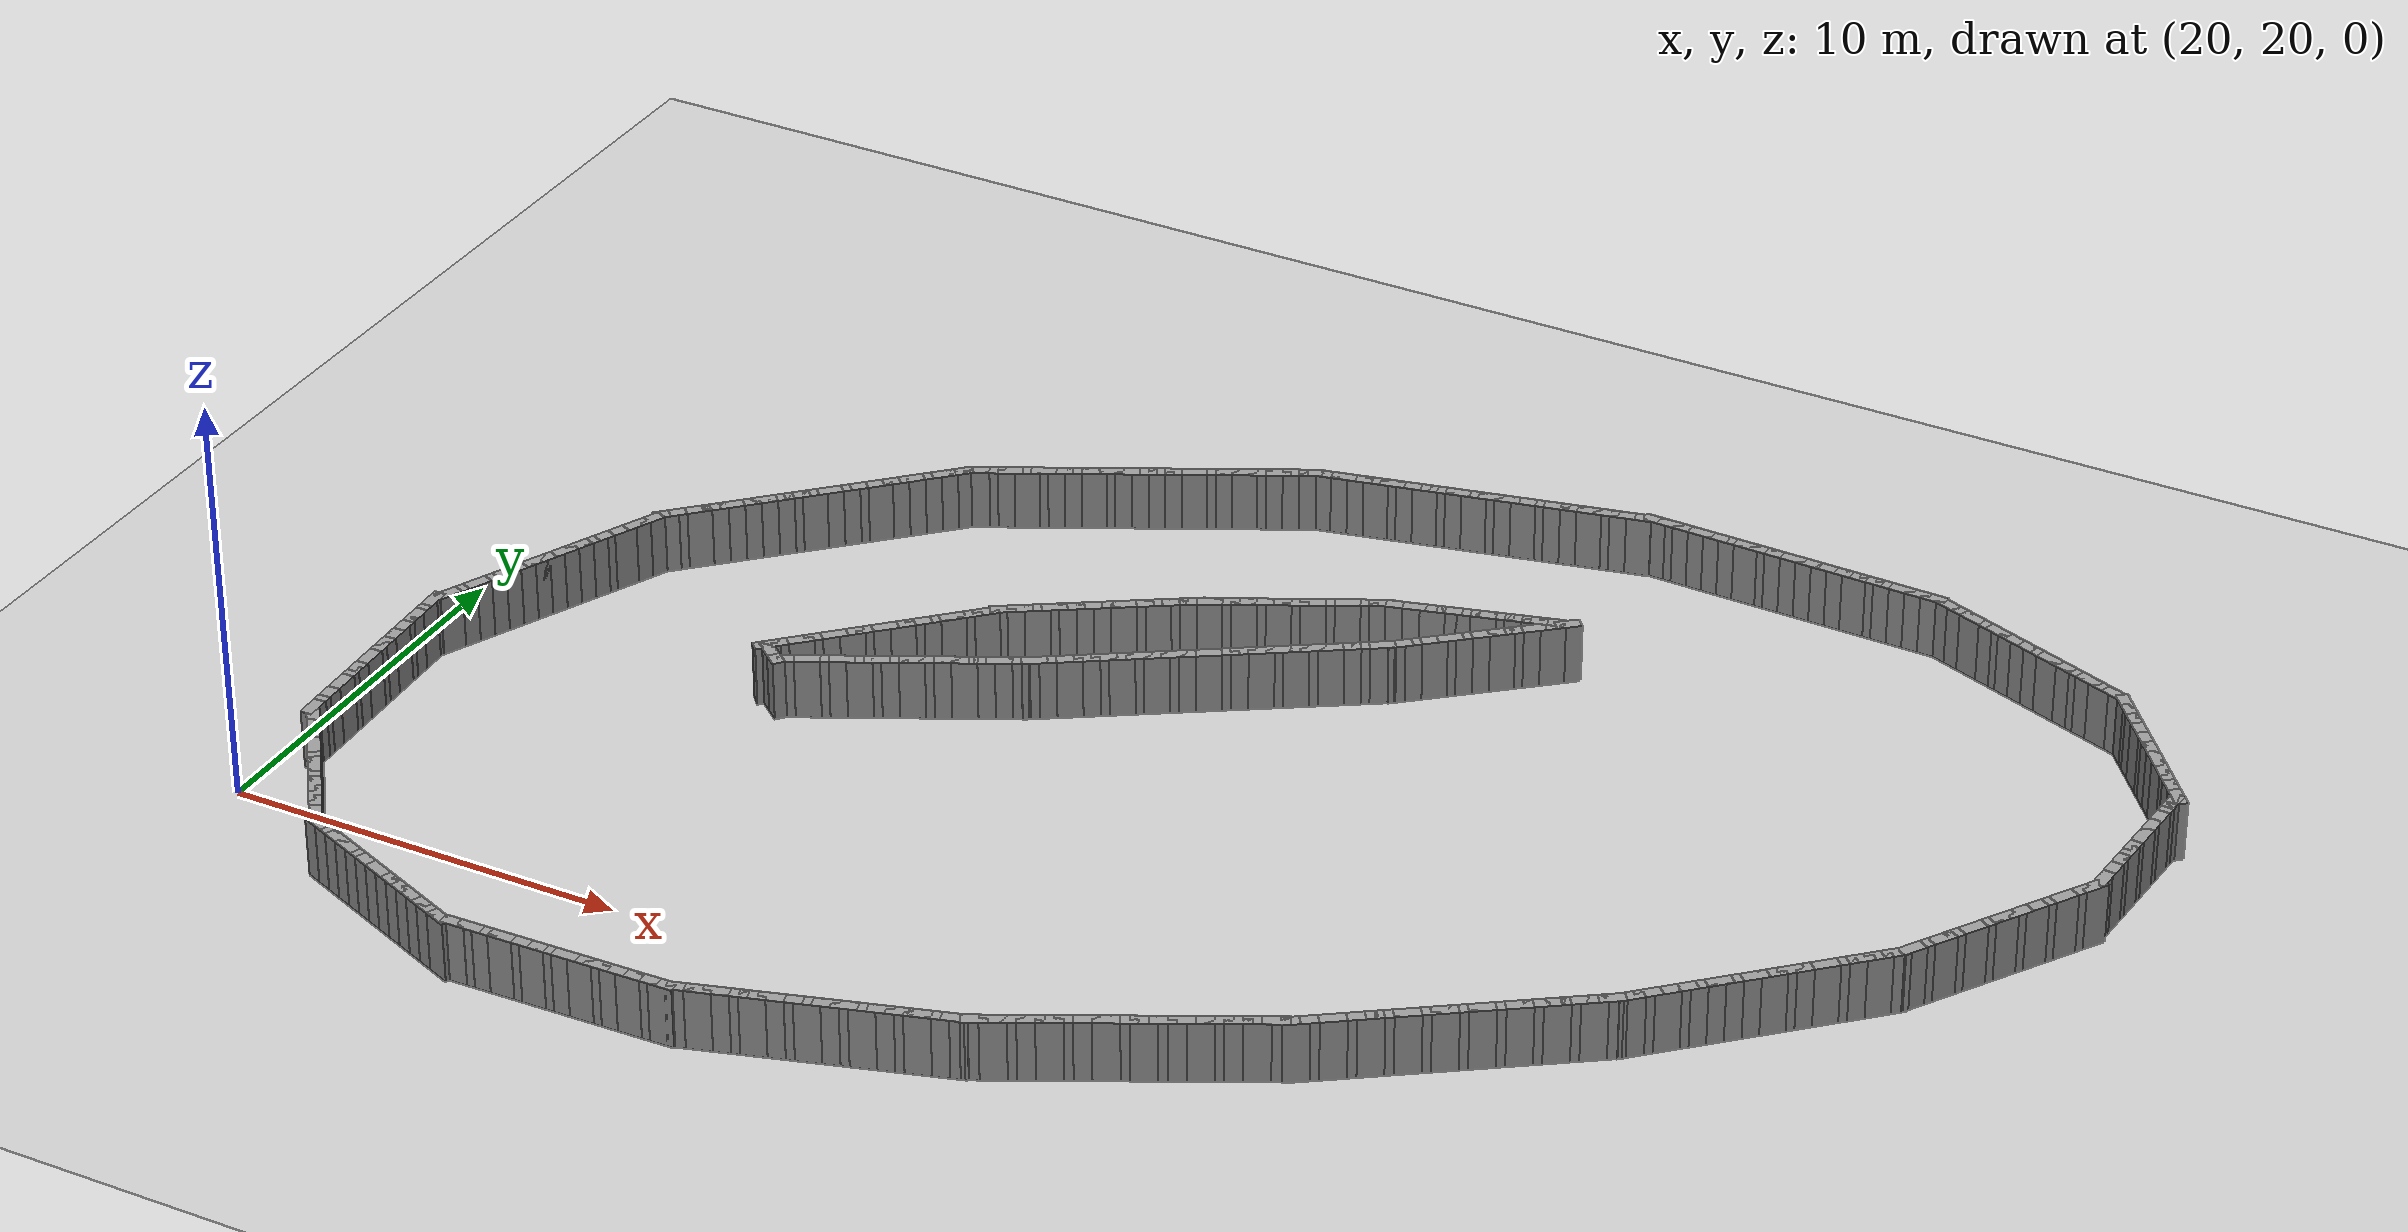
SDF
<?xml version="1.0" ?>
<sdf version="1.5">
  <world name="test_l_shape">
    <include><uri>model://sun</uri></include>
    <include><uri>model://ground_plane</uri></include>
    <model name="curbL_0">
      <static>true</static>
      <pose>59.346 38.500 0.750 0 0 2.252</pose>
      <link name="link">
        <collision name="col">
          <geometry><box><size>0.600 0.300 1.500</size></box></geometry>
        </collision>
        <visual name="vis">
          <geometry><box><size>0.600 0.300 1.500</size></box></geometry>
          <material>
            <ambient>0.6 0.6 0.6 1</ambient>
            <diffuse>0.6 0.6 0.6 1</diffuse>
          </material>
        </visual>
      </link>
    </model>
    <model name="curbL_1">
      <static>true</static>
      <pose>59.094 38.811 0.750 0 0 2.252</pose>
      <link name="link">
        <collision name="col">
          <geometry><box><size>0.600 0.300 1.500</size></box></geometry>
        </collision>
        <visual name="vis">
          <geometry><box><size>0.600 0.300 1.500</size></box></geometry>
          <material>
            <ambient>0.6 0.6 0.6 1</ambient>
            <diffuse>0.6 0.6 0.6 1</diffuse>
          </material>
        </visual>
      </link>
    </model>
    <model name="curbL_2">
      <static>true</static>
      <pose>58.842 39.122 0.750 0 0 2.252</pose>
      <link name="link">
        <collision name="col">
          <geometry><box><size>0.600 0.300 1.500</size></box></geometry>
        </collision>
        <visual name="vis">
          <geometry><box><size>0.600 0.300 1.500</size></box></geometry>
          <material>
            <ambient>0.6 0.6 0.6 1</ambient>
            <diffuse>0.6 0.6 0.6 1</diffuse>
          </material>
        </visual>
      </link>
    </model>
    <model name="curbL_3">
      <static>true</static>
      <pose>58.590 39.432 0.750 0 0 2.252</pose>
      <link name="link">
        <collision name="col">
          <geometry><box><size>0.600 0.300 1.500</size></box></geometry>
        </collision>
        <visual name="vis">
          <geometry><box><size>0.600 0.300 1.500</size></box></geometry>
          <material>
            <ambient>0.6 0.6 0.6 1</ambient>
            <diffuse>0.6 0.6 0.6 1</diffuse>
          </material>
        </visual>
      </link>
    </model>
    <model name="curbL_4">
      <static>true</static>
      <pose>58.338 39.743 0.750 0 0 2.252</pose>
      <link name="link">
        <collision name="col">
          <geometry><box><size>0.600 0.300 1.500</size></box></geometry>
        </collision>
        <visual name="vis">
          <geometry><box><size>0.600 0.300 1.500</size></box></geometry>
          <material>
            <ambient>0.6 0.6 0.6 1</ambient>
            <diffuse>0.6 0.6 0.6 1</diffuse>
          </material>
        </visual>
      </link>
    </model>
    <model name="curbL_5">
      <static>true</static>
      <pose>58.086 40.054 0.750 0 0 2.252</pose>
      <link name="link">
        <collision name="col">
          <geometry><box><size>0.600 0.300 1.500</size></box></geometry>
        </collision>
        <visual name="vis">
          <geometry><box><size>0.600 0.300 1.500</size></box></geometry>
          <material>
            <ambient>0.6 0.6 0.6 1</ambient>
            <diffuse>0.6 0.6 0.6 1</diffuse>
          </material>
        </visual>
      </link>
    </model>
    <model name="curbL_6">
      <static>true</static>
      <pose>57.834 40.365 0.750 0 0 2.252</pose>
      <link name="link">
        <collision name="col">
          <geometry><box><size>0.600 0.300 1.500</size></box></geometry>
        </collision>
        <visual name="vis">
          <geometry><box><size>0.600 0.300 1.500</size></box></geometry>
          <material>
            <ambient>0.6 0.6 0.6 1</ambient>
            <diffuse>0.6 0.6 0.6 1</diffuse>
          </material>
        </visual>
      </link>
    </model>
    <model name="curbL_7">
      <static>true</static>
      <pose>57.582 40.675 0.750 0 0 2.252</pose>
      <link name="link">
        <collision name="col">
          <geometry><box><size>0.600 0.300 1.500</size></box></geometry>
        </collision>
        <visual name="vis">
          <geometry><box><size>0.600 0.300 1.500</size></box></geometry>
          <material>
            <ambient>0.6 0.6 0.6 1</ambient>
            <diffuse>0.6 0.6 0.6 1</diffuse>
          </material>
        </visual>
      </link>
    </model>
    <model name="curbL_8">
      <static>true</static>
      <pose>57.330 40.986 0.750 0 0 2.252</pose>
      <link name="link">
        <collision name="col">
          <geometry><box><size>0.600 0.300 1.500</size></box></geometry>
        </collision>
        <visual name="vis">
          <geometry><box><size>0.600 0.300 1.500</size></box></geometry>
          <material>
            <ambient>0.6 0.6 0.6 1</ambient>
            <diffuse>0.6 0.6 0.6 1</diffuse>
          </material>
        </visual>
      </link>
    </model>
    <model name="curbL_9">
      <static>true</static>
      <pose>57.078 41.297 0.750 0 0 2.252</pose>
      <link name="link">
        <collision name="col">
          <geometry><box><size>0.600 0.300 1.500</size></box></geometry>
        </collision>
        <visual name="vis">
          <geometry><box><size>0.600 0.300 1.500</size></box></geometry>
          <material>
            <ambient>0.6 0.6 0.6 1</ambient>
            <diffuse>0.6 0.6 0.6 1</diffuse>
          </material>
        </visual>
      </link>
    </model>
    <model name="curbL_10">
      <static>true</static>
      <pose>56.826 41.607 0.750 0 0 2.252</pose>
      <link name="link">
        <collision name="col">
          <geometry><box><size>0.600 0.300 1.500</size></box></geometry>
        </collision>
        <visual name="vis">
          <geometry><box><size>0.600 0.300 1.500</size></box></geometry>
          <material>
            <ambient>0.6 0.6 0.6 1</ambient>
            <diffuse>0.6 0.6 0.6 1</diffuse>
          </material>
        </visual>
      </link>
    </model>
    <model name="curbL_11">
      <static>true</static>
      <pose>56.508 41.824 0.750 0 0 2.795</pose>
      <link name="link">
        <collision name="col">
          <geometry><box><size>0.600 0.300 1.500</size></box></geometry>
        </collision>
        <visual name="vis">
          <geometry><box><size>0.600 0.300 1.500</size></box></geometry>
          <material>
            <ambient>0.6 0.6 0.6 1</ambient>
            <diffuse>0.6 0.6 0.6 1</diffuse>
          </material>
        </visual>
      </link>
    </model>
    <model name="curbL_12">
      <static>true</static>
      <pose>56.131 41.960 0.750 0 0 2.795</pose>
      <link name="link">
        <collision name="col">
          <geometry><box><size>0.600 0.300 1.500</size></box></geometry>
        </collision>
        <visual name="vis">
          <geometry><box><size>0.600 0.300 1.500</size></box></geometry>
          <material>
            <ambient>0.6 0.6 0.6 1</ambient>
            <diffuse>0.6 0.6 0.6 1</diffuse>
          </material>
        </visual>
      </link>
    </model>
    <model name="curbL_13">
      <static>true</static>
      <pose>55.755 42.096 0.750 0 0 2.795</pose>
      <link name="link">
        <collision name="col">
          <geometry><box><size>0.600 0.300 1.500</size></box></geometry>
        </collision>
        <visual name="vis">
          <geometry><box><size>0.600 0.300 1.500</size></box></geometry>
          <material>
            <ambient>0.6 0.6 0.6 1</ambient>
            <diffuse>0.6 0.6 0.6 1</diffuse>
          </material>
        </visual>
      </link>
    </model>
    <model name="curbL_14">
      <static>true</static>
      <pose>55.379 42.232 0.750 0 0 2.795</pose>
      <link name="link">
        <collision name="col">
          <geometry><box><size>0.600 0.300 1.500</size></box></geometry>
        </collision>
        <visual name="vis">
          <geometry><box><size>0.600 0.300 1.500</size></box></geometry>
          <material>
            <ambient>0.6 0.6 0.6 1</ambient>
            <diffuse>0.6 0.6 0.6 1</diffuse>
          </material>
        </visual>
      </link>
    </model>
    <model name="curbL_15">
      <static>true</static>
      <pose>55.003 42.367 0.750 0 0 2.795</pose>
      <link name="link">
        <collision name="col">
          <geometry><box><size>0.600 0.300 1.500</size></box></geometry>
        </collision>
        <visual name="vis">
          <geometry><box><size>0.600 0.300 1.500</size></box></geometry>
          <material>
            <ambient>0.6 0.6 0.6 1</ambient>
            <diffuse>0.6 0.6 0.6 1</diffuse>
          </material>
        </visual>
      </link>
    </model>
    <model name="curbL_16">
      <static>true</static>
      <pose>54.626 42.503 0.750 0 0 2.795</pose>
      <link name="link">
        <collision name="col">
          <geometry><box><size>0.600 0.300 1.500</size></box></geometry>
        </collision>
        <visual name="vis">
          <geometry><box><size>0.600 0.300 1.500</size></box></geometry>
          <material>
            <ambient>0.6 0.6 0.6 1</ambient>
            <diffuse>0.6 0.6 0.6 1</diffuse>
          </material>
        </visual>
      </link>
    </model>
    <model name="curbL_17">
      <static>true</static>
      <pose>54.250 42.639 0.750 0 0 2.795</pose>
      <link name="link">
        <collision name="col">
          <geometry><box><size>0.600 0.300 1.500</size></box></geometry>
        </collision>
        <visual name="vis">
          <geometry><box><size>0.600 0.300 1.500</size></box></geometry>
          <material>
            <ambient>0.6 0.6 0.6 1</ambient>
            <diffuse>0.6 0.6 0.6 1</diffuse>
          </material>
        </visual>
      </link>
    </model>
    <model name="curbL_18">
      <static>true</static>
      <pose>53.874 42.775 0.750 0 0 2.795</pose>
      <link name="link">
        <collision name="col">
          <geometry><box><size>0.600 0.300 1.500</size></box></geometry>
        </collision>
        <visual name="vis">
          <geometry><box><size>0.600 0.300 1.500</size></box></geometry>
          <material>
            <ambient>0.6 0.6 0.6 1</ambient>
            <diffuse>0.6 0.6 0.6 1</diffuse>
          </material>
        </visual>
      </link>
    </model>
    <model name="curbL_19">
      <static>true</static>
      <pose>53.498 42.911 0.750 0 0 2.795</pose>
      <link name="link">
        <collision name="col">
          <geometry><box><size>0.600 0.300 1.500</size></box></geometry>
        </collision>
        <visual name="vis">
          <geometry><box><size>0.600 0.300 1.500</size></box></geometry>
          <material>
            <ambient>0.6 0.6 0.6 1</ambient>
            <diffuse>0.6 0.6 0.6 1</diffuse>
          </material>
        </visual>
      </link>
    </model>
    <model name="curbL_20">
      <static>true</static>
      <pose>53.122 43.047 0.750 0 0 2.795</pose>
      <link name="link">
        <collision name="col">
          <geometry><box><size>0.600 0.300 1.500</size></box></geometry>
        </collision>
        <visual name="vis">
          <geometry><box><size>0.600 0.300 1.500</size></box></geometry>
          <material>
            <ambient>0.6 0.6 0.6 1</ambient>
            <diffuse>0.6 0.6 0.6 1</diffuse>
          </material>
        </visual>
      </link>
    </model>
    <model name="curbL_21">
      <static>true</static>
      <pose>52.745 43.183 0.750 0 0 2.795</pose>
      <link name="link">
        <collision name="col">
          <geometry><box><size>0.600 0.300 1.500</size></box></geometry>
        </collision>
        <visual name="vis">
          <geometry><box><size>0.600 0.300 1.500</size></box></geometry>
          <material>
            <ambient>0.6 0.6 0.6 1</ambient>
            <diffuse>0.6 0.6 0.6 1</diffuse>
          </material>
        </visual>
      </link>
    </model>
    <model name="curbL_22">
      <static>true</static>
      <pose>52.369 43.318 0.750 0 0 2.795</pose>
      <link name="link">
        <collision name="col">
          <geometry><box><size>0.600 0.300 1.500</size></box></geometry>
        </collision>
        <visual name="vis">
          <geometry><box><size>0.600 0.300 1.500</size></box></geometry>
          <material>
            <ambient>0.6 0.6 0.6 1</ambient>
            <diffuse>0.6 0.6 0.6 1</diffuse>
          </material>
        </visual>
      </link>
    </model>
    <model name="curbL_23">
      <static>true</static>
      <pose>51.993 43.454 0.750 0 0 2.795</pose>
      <link name="link">
        <collision name="col">
          <geometry><box><size>0.600 0.300 1.500</size></box></geometry>
        </collision>
        <visual name="vis">
          <geometry><box><size>0.600 0.300 1.500</size></box></geometry>
          <material>
            <ambient>0.6 0.6 0.6 1</ambient>
            <diffuse>0.6 0.6 0.6 1</diffuse>
          </material>
        </visual>
      </link>
    </model>
    <model name="curbL_24">
      <static>true</static>
      <pose>51.617 43.590 0.750 0 0 2.795</pose>
      <link name="link">
        <collision name="col">
          <geometry><box><size>0.600 0.300 1.500</size></box></geometry>
        </collision>
        <visual name="vis">
          <geometry><box><size>0.600 0.300 1.500</size></box></geometry>
          <material>
            <ambient>0.6 0.6 0.6 1</ambient>
            <diffuse>0.6 0.6 0.6 1</diffuse>
          </material>
        </visual>
      </link>
    </model>
    <model name="curbL_25">
      <static>true</static>
      <pose>51.233 43.686 0.750 0 0 3.122</pose>
      <link name="link">
        <collision name="col">
          <geometry><box><size>0.600 0.300 1.500</size></box></geometry>
        </collision>
        <visual name="vis">
          <geometry><box><size>0.600 0.300 1.500</size></box></geometry>
          <material>
            <ambient>0.6 0.6 0.6 1</ambient>
            <diffuse>0.6 0.6 0.6 1</diffuse>
          </material>
        </visual>
      </link>
    </model>
    <model name="curbL_26">
      <static>true</static>
      <pose>50.833 43.694 0.750 0 0 3.122</pose>
      <link name="link">
        <collision name="col">
          <geometry><box><size>0.600 0.300 1.500</size></box></geometry>
        </collision>
        <visual name="vis">
          <geometry><box><size>0.600 0.300 1.500</size></box></geometry>
          <material>
            <ambient>0.6 0.6 0.6 1</ambient>
            <diffuse>0.6 0.6 0.6 1</diffuse>
          </material>
        </visual>
      </link>
    </model>
    <model name="curbL_27">
      <static>true</static>
      <pose>50.433 43.702 0.750 0 0 3.122</pose>
      <link name="link">
        <collision name="col">
          <geometry><box><size>0.600 0.300 1.500</size></box></geometry>
        </collision>
        <visual name="vis">
          <geometry><box><size>0.600 0.300 1.500</size></box></geometry>
          <material>
            <ambient>0.6 0.6 0.6 1</ambient>
            <diffuse>0.6 0.6 0.6 1</diffuse>
          </material>
        </visual>
      </link>
    </model>
    <model name="curbL_28">
      <static>true</static>
      <pose>50.033 43.710 0.750 0 0 3.122</pose>
      <link name="link">
        <collision name="col">
          <geometry><box><size>0.600 0.300 1.500</size></box></geometry>
        </collision>
        <visual name="vis">
          <geometry><box><size>0.600 0.300 1.500</size></box></geometry>
          <material>
            <ambient>0.6 0.6 0.6 1</ambient>
            <diffuse>0.6 0.6 0.6 1</diffuse>
          </material>
        </visual>
      </link>
    </model>
    <model name="curbL_29">
      <static>true</static>
      <pose>49.633 43.718 0.750 0 0 3.122</pose>
      <link name="link">
        <collision name="col">
          <geometry><box><size>0.600 0.300 1.500</size></box></geometry>
        </collision>
        <visual name="vis">
          <geometry><box><size>0.600 0.300 1.500</size></box></geometry>
          <material>
            <ambient>0.6 0.6 0.6 1</ambient>
            <diffuse>0.6 0.6 0.6 1</diffuse>
          </material>
        </visual>
      </link>
    </model>
    <model name="curbL_30">
      <static>true</static>
      <pose>49.234 43.725 0.750 0 0 3.122</pose>
      <link name="link">
        <collision name="col">
          <geometry><box><size>0.600 0.300 1.500</size></box></geometry>
        </collision>
        <visual name="vis">
          <geometry><box><size>0.600 0.300 1.500</size></box></geometry>
          <material>
            <ambient>0.6 0.6 0.6 1</ambient>
            <diffuse>0.6 0.6 0.6 1</diffuse>
          </material>
        </visual>
      </link>
    </model>
    <model name="curbL_31">
      <static>true</static>
      <pose>48.834 43.733 0.750 0 0 3.122</pose>
      <link name="link">
        <collision name="col">
          <geometry><box><size>0.600 0.300 1.500</size></box></geometry>
        </collision>
        <visual name="vis">
          <geometry><box><size>0.600 0.300 1.500</size></box></geometry>
          <material>
            <ambient>0.6 0.6 0.6 1</ambient>
            <diffuse>0.6 0.6 0.6 1</diffuse>
          </material>
        </visual>
      </link>
    </model>
    <model name="curbL_32">
      <static>true</static>
      <pose>48.434 43.741 0.750 0 0 3.122</pose>
      <link name="link">
        <collision name="col">
          <geometry><box><size>0.600 0.300 1.500</size></box></geometry>
        </collision>
        <visual name="vis">
          <geometry><box><size>0.600 0.300 1.500</size></box></geometry>
          <material>
            <ambient>0.6 0.6 0.6 1</ambient>
            <diffuse>0.6 0.6 0.6 1</diffuse>
          </material>
        </visual>
      </link>
    </model>
    <model name="curbL_33">
      <static>true</static>
      <pose>48.034 43.749 0.750 0 0 3.122</pose>
      <link name="link">
        <collision name="col">
          <geometry><box><size>0.600 0.300 1.500</size></box></geometry>
        </collision>
        <visual name="vis">
          <geometry><box><size>0.600 0.300 1.500</size></box></geometry>
          <material>
            <ambient>0.6 0.6 0.6 1</ambient>
            <diffuse>0.6 0.6 0.6 1</diffuse>
          </material>
        </visual>
      </link>
    </model>
    <model name="curbL_34">
      <static>true</static>
      <pose>47.634 43.757 0.750 0 0 3.122</pose>
      <link name="link">
        <collision name="col">
          <geometry><box><size>0.600 0.300 1.500</size></box></geometry>
        </collision>
        <visual name="vis">
          <geometry><box><size>0.600 0.300 1.500</size></box></geometry>
          <material>
            <ambient>0.6 0.6 0.6 1</ambient>
            <diffuse>0.6 0.6 0.6 1</diffuse>
          </material>
        </visual>
      </link>
    </model>
    <model name="curbL_35">
      <static>true</static>
      <pose>47.234 43.765 0.750 0 0 3.122</pose>
      <link name="link">
        <collision name="col">
          <geometry><box><size>0.600 0.300 1.500</size></box></geometry>
        </collision>
        <visual name="vis">
          <geometry><box><size>0.600 0.300 1.500</size></box></geometry>
          <material>
            <ambient>0.6 0.6 0.6 1</ambient>
            <diffuse>0.6 0.6 0.6 1</diffuse>
          </material>
        </visual>
      </link>
    </model>
    <model name="curbL_36">
      <static>true</static>
      <pose>46.834 43.773 0.750 0 0 3.122</pose>
      <link name="link">
        <collision name="col">
          <geometry><box><size>0.600 0.300 1.500</size></box></geometry>
        </collision>
        <visual name="vis">
          <geometry><box><size>0.600 0.300 1.500</size></box></geometry>
          <material>
            <ambient>0.6 0.6 0.6 1</ambient>
            <diffuse>0.6 0.6 0.6 1</diffuse>
          </material>
        </visual>
      </link>
    </model>
    <model name="curbL_37">
      <static>true</static>
      <pose>46.434 43.780 0.750 0 0 3.122</pose>
      <link name="link">
        <collision name="col">
          <geometry><box><size>0.600 0.300 1.500</size></box></geometry>
        </collision>
        <visual name="vis">
          <geometry><box><size>0.600 0.300 1.500</size></box></geometry>
          <material>
            <ambient>0.6 0.6 0.6 1</ambient>
            <diffuse>0.6 0.6 0.6 1</diffuse>
          </material>
        </visual>
      </link>
    </model>
    <model name="curbL_38">
      <static>true</static>
      <pose>46.034 43.788 0.750 0 0 3.122</pose>
      <link name="link">
        <collision name="col">
          <geometry><box><size>0.600 0.300 1.500</size></box></geometry>
        </collision>
        <visual name="vis">
          <geometry><box><size>0.600 0.300 1.500</size></box></geometry>
          <material>
            <ambient>0.6 0.6 0.6 1</ambient>
            <diffuse>0.6 0.6 0.6 1</diffuse>
          </material>
        </visual>
      </link>
    </model>
    <model name="curbL_39">
      <static>true</static>
      <pose>45.634 43.796 0.750 0 0 3.122</pose>
      <link name="link">
        <collision name="col">
          <geometry><box><size>0.600 0.300 1.500</size></box></geometry>
        </collision>
        <visual name="vis">
          <geometry><box><size>0.600 0.300 1.500</size></box></geometry>
          <material>
            <ambient>0.6 0.6 0.6 1</ambient>
            <diffuse>0.6 0.6 0.6 1</diffuse>
          </material>
        </visual>
      </link>
    </model>
    <model name="curbL_40">
      <static>true</static>
      <pose>45.234 43.804 0.750 0 0 3.122</pose>
      <link name="link">
        <collision name="col">
          <geometry><box><size>0.600 0.300 1.500</size></box></geometry>
        </collision>
        <visual name="vis">
          <geometry><box><size>0.600 0.300 1.500</size></box></geometry>
          <material>
            <ambient>0.6 0.6 0.6 1</ambient>
            <diffuse>0.6 0.6 0.6 1</diffuse>
          </material>
        </visual>
      </link>
    </model>
    <model name="curbL_41">
      <static>true</static>
      <pose>44.834 43.812 0.750 0 0 3.122</pose>
      <link name="link">
        <collision name="col">
          <geometry><box><size>0.600 0.300 1.500</size></box></geometry>
        </collision>
        <visual name="vis">
          <geometry><box><size>0.600 0.300 1.500</size></box></geometry>
          <material>
            <ambient>0.6 0.6 0.6 1</ambient>
            <diffuse>0.6 0.6 0.6 1</diffuse>
          </material>
        </visual>
      </link>
    </model>
    <model name="curbL_42">
      <static>true</static>
      <pose>44.434 43.820 0.750 0 0 3.122</pose>
      <link name="link">
        <collision name="col">
          <geometry><box><size>0.600 0.300 1.500</size></box></geometry>
        </collision>
        <visual name="vis">
          <geometry><box><size>0.600 0.300 1.500</size></box></geometry>
          <material>
            <ambient>0.6 0.6 0.6 1</ambient>
            <diffuse>0.6 0.6 0.6 1</diffuse>
          </material>
        </visual>
      </link>
    </model>
    <model name="curbL_43">
      <static>true</static>
      <pose>44.035 43.827 0.750 0 0 3.122</pose>
      <link name="link">
        <collision name="col">
          <geometry><box><size>0.600 0.300 1.500</size></box></geometry>
        </collision>
        <visual name="vis">
          <geometry><box><size>0.600 0.300 1.500</size></box></geometry>
          <material>
            <ambient>0.6 0.6 0.6 1</ambient>
            <diffuse>0.6 0.6 0.6 1</diffuse>
          </material>
        </visual>
      </link>
    </model>
    <model name="curbL_44">
      <static>true</static>
      <pose>43.645 43.739 0.750 0 0 -2.911</pose>
      <link name="link">
        <collision name="col">
          <geometry><box><size>0.600 0.300 1.500</size></box></geometry>
        </collision>
        <visual name="vis">
          <geometry><box><size>0.600 0.300 1.500</size></box></geometry>
          <material>
            <ambient>0.6 0.6 0.6 1</ambient>
            <diffuse>0.6 0.6 0.6 1</diffuse>
          </material>
        </visual>
      </link>
    </model>
    <model name="curbL_45">
      <static>true</static>
      <pose>43.255 43.648 0.750 0 0 -2.911</pose>
      <link name="link">
        <collision name="col">
          <geometry><box><size>0.600 0.300 1.500</size></box></geometry>
        </collision>
        <visual name="vis">
          <geometry><box><size>0.600 0.300 1.500</size></box></geometry>
          <material>
            <ambient>0.6 0.6 0.6 1</ambient>
            <diffuse>0.6 0.6 0.6 1</diffuse>
          </material>
        </visual>
      </link>
    </model>
    <model name="curbL_46">
      <static>true</static>
      <pose>42.866 43.557 0.750 0 0 -2.911</pose>
      <link name="link">
        <collision name="col">
          <geometry><box><size>0.600 0.300 1.500</size></box></geometry>
        </collision>
        <visual name="vis">
          <geometry><box><size>0.600 0.300 1.500</size></box></geometry>
          <material>
            <ambient>0.6 0.6 0.6 1</ambient>
            <diffuse>0.6 0.6 0.6 1</diffuse>
          </material>
        </visual>
      </link>
    </model>
    <model name="curbL_47">
      <static>true</static>
      <pose>42.476 43.465 0.750 0 0 -2.911</pose>
      <link name="link">
        <collision name="col">
          <geometry><box><size>0.600 0.300 1.500</size></box></geometry>
        </collision>
        <visual name="vis">
          <geometry><box><size>0.600 0.300 1.500</size></box></geometry>
          <material>
            <ambient>0.6 0.6 0.6 1</ambient>
            <diffuse>0.6 0.6 0.6 1</diffuse>
          </material>
        </visual>
      </link>
    </model>
    <model name="curbL_48">
      <static>true</static>
      <pose>42.087 43.374 0.750 0 0 -2.911</pose>
      <link name="link">
        <collision name="col">
          <geometry><box><size>0.600 0.300 1.500</size></box></geometry>
        </collision>
        <visual name="vis">
          <geometry><box><size>0.600 0.300 1.500</size></box></geometry>
          <material>
            <ambient>0.6 0.6 0.6 1</ambient>
            <diffuse>0.6 0.6 0.6 1</diffuse>
          </material>
        </visual>
      </link>
    </model>
    <model name="curbL_49">
      <static>true</static>
      <pose>41.698 43.283 0.750 0 0 -2.911</pose>
      <link name="link">
        <collision name="col">
          <geometry><box><size>0.600 0.300 1.500</size></box></geometry>
        </collision>
        <visual name="vis">
          <geometry><box><size>0.600 0.300 1.500</size></box></geometry>
          <material>
            <ambient>0.6 0.6 0.6 1</ambient>
            <diffuse>0.6 0.6 0.6 1</diffuse>
          </material>
        </visual>
      </link>
    </model>
    <model name="curbL_50">
      <static>true</static>
      <pose>41.308 43.192 0.750 0 0 -2.911</pose>
      <link name="link">
        <collision name="col">
          <geometry><box><size>0.600 0.300 1.500</size></box></geometry>
        </collision>
        <visual name="vis">
          <geometry><box><size>0.600 0.300 1.500</size></box></geometry>
          <material>
            <ambient>0.6 0.6 0.6 1</ambient>
            <diffuse>0.6 0.6 0.6 1</diffuse>
          </material>
        </visual>
      </link>
    </model>
    <model name="curbL_51">
      <static>true</static>
      <pose>40.919 43.100 0.750 0 0 -2.911</pose>
      <link name="link">
        <collision name="col">
          <geometry><box><size>0.600 0.300 1.500</size></box></geometry>
        </collision>
        <visual name="vis">
          <geometry><box><size>0.600 0.300 1.500</size></box></geometry>
          <material>
            <ambient>0.6 0.6 0.6 1</ambient>
            <diffuse>0.6 0.6 0.6 1</diffuse>
          </material>
        </visual>
      </link>
    </model>
    <model name="curbL_52">
      <static>true</static>
      <pose>40.529 43.009 0.750 0 0 -2.911</pose>
      <link name="link">
        <collision name="col">
          <geometry><box><size>0.600 0.300 1.500</size></box></geometry>
        </collision>
        <visual name="vis">
          <geometry><box><size>0.600 0.300 1.500</size></box></geometry>
          <material>
            <ambient>0.6 0.6 0.6 1</ambient>
            <diffuse>0.6 0.6 0.6 1</diffuse>
          </material>
        </visual>
      </link>
    </model>
    <model name="curbL_53">
      <static>true</static>
      <pose>40.140 42.918 0.750 0 0 -2.911</pose>
      <link name="link">
        <collision name="col">
          <geometry><box><size>0.600 0.300 1.500</size></box></geometry>
        </collision>
        <visual name="vis">
          <geometry><box><size>0.600 0.300 1.500</size></box></geometry>
          <material>
            <ambient>0.6 0.6 0.6 1</ambient>
            <diffuse>0.6 0.6 0.6 1</diffuse>
          </material>
        </visual>
      </link>
    </model>
    <model name="curbL_54">
      <static>true</static>
      <pose>39.750 42.826 0.750 0 0 -2.911</pose>
      <link name="link">
        <collision name="col">
          <geometry><box><size>0.600 0.300 1.500</size></box></geometry>
        </collision>
        <visual name="vis">
          <geometry><box><size>0.600 0.300 1.500</size></box></geometry>
          <material>
            <ambient>0.6 0.6 0.6 1</ambient>
            <diffuse>0.6 0.6 0.6 1</diffuse>
          </material>
        </visual>
      </link>
    </model>
    <model name="curbL_55">
      <static>true</static>
      <pose>39.361 42.735 0.750 0 0 -2.911</pose>
      <link name="link">
        <collision name="col">
          <geometry><box><size>0.600 0.300 1.500</size></box></geometry>
        </collision>
        <visual name="vis">
          <geometry><box><size>0.600 0.300 1.500</size></box></geometry>
          <material>
            <ambient>0.6 0.6 0.6 1</ambient>
            <diffuse>0.6 0.6 0.6 1</diffuse>
          </material>
        </visual>
      </link>
    </model>
    <model name="curbL_56">
      <static>true</static>
      <pose>38.971 42.644 0.750 0 0 -2.911</pose>
      <link name="link">
        <collision name="col">
          <geometry><box><size>0.600 0.300 1.500</size></box></geometry>
        </collision>
        <visual name="vis">
          <geometry><box><size>0.600 0.300 1.500</size></box></geometry>
          <material>
            <ambient>0.6 0.6 0.6 1</ambient>
            <diffuse>0.6 0.6 0.6 1</diffuse>
          </material>
        </visual>
      </link>
    </model>
    <model name="curbL_57">
      <static>true</static>
      <pose>38.582 42.552 0.750 0 0 -2.911</pose>
      <link name="link">
        <collision name="col">
          <geometry><box><size>0.600 0.300 1.500</size></box></geometry>
        </collision>
        <visual name="vis">
          <geometry><box><size>0.600 0.300 1.500</size></box></geometry>
          <material>
            <ambient>0.6 0.6 0.6 1</ambient>
            <diffuse>0.6 0.6 0.6 1</diffuse>
          </material>
        </visual>
      </link>
    </model>
    <model name="curbL_58">
      <static>true</static>
      <pose>38.193 42.461 0.750 0 0 -2.911</pose>
      <link name="link">
        <collision name="col">
          <geometry><box><size>0.600 0.300 1.500</size></box></geometry>
        </collision>
        <visual name="vis">
          <geometry><box><size>0.600 0.300 1.500</size></box></geometry>
          <material>
            <ambient>0.6 0.6 0.6 1</ambient>
            <diffuse>0.6 0.6 0.6 1</diffuse>
          </material>
        </visual>
      </link>
    </model>
    <model name="curbL_59">
      <static>true</static>
      <pose>37.803 42.370 0.750 0 0 -2.911</pose>
      <link name="link">
        <collision name="col">
          <geometry><box><size>0.600 0.300 1.500</size></box></geometry>
        </collision>
        <visual name="vis">
          <geometry><box><size>0.600 0.300 1.500</size></box></geometry>
          <material>
            <ambient>0.6 0.6 0.6 1</ambient>
            <diffuse>0.6 0.6 0.6 1</diffuse>
          </material>
        </visual>
      </link>
    </model>
    <model name="curbL_60">
      <static>true</static>
      <pose>37.414 42.278 0.750 0 0 -2.911</pose>
      <link name="link">
        <collision name="col">
          <geometry><box><size>0.600 0.300 1.500</size></box></geometry>
        </collision>
        <visual name="vis">
          <geometry><box><size>0.600 0.300 1.500</size></box></geometry>
          <material>
            <ambient>0.6 0.6 0.6 1</ambient>
            <diffuse>0.6 0.6 0.6 1</diffuse>
          </material>
        </visual>
      </link>
    </model>
    <model name="curbL_61">
      <static>true</static>
      <pose>37.024 42.187 0.750 0 0 -2.911</pose>
      <link name="link">
        <collision name="col">
          <geometry><box><size>0.600 0.300 1.500</size></box></geometry>
        </collision>
        <visual name="vis">
          <geometry><box><size>0.600 0.300 1.500</size></box></geometry>
          <material>
            <ambient>0.6 0.6 0.6 1</ambient>
            <diffuse>0.6 0.6 0.6 1</diffuse>
          </material>
        </visual>
      </link>
    </model>
    <model name="curbL_62">
      <static>true</static>
      <pose>36.635 42.096 0.750 0 0 -2.911</pose>
      <link name="link">
        <collision name="col">
          <geometry><box><size>0.600 0.300 1.500</size></box></geometry>
        </collision>
        <visual name="vis">
          <geometry><box><size>0.600 0.300 1.500</size></box></geometry>
          <material>
            <ambient>0.6 0.6 0.6 1</ambient>
            <diffuse>0.6 0.6 0.6 1</diffuse>
          </material>
        </visual>
      </link>
    </model>
    <model name="curbL_63">
      <static>true</static>
      <pose>36.245 42.005 0.750 0 0 -2.911</pose>
      <link name="link">
        <collision name="col">
          <geometry><box><size>0.600 0.300 1.500</size></box></geometry>
        </collision>
        <visual name="vis">
          <geometry><box><size>0.600 0.300 1.500</size></box></geometry>
          <material>
            <ambient>0.6 0.6 0.6 1</ambient>
            <diffuse>0.6 0.6 0.6 1</diffuse>
          </material>
        </visual>
      </link>
    </model>
    <model name="curbL_64">
      <static>true</static>
      <pose>35.867 41.885 0.750 0 0 -2.661</pose>
      <link name="link">
        <collision name="col">
          <geometry><box><size>0.600 0.300 1.500</size></box></geometry>
        </collision>
        <visual name="vis">
          <geometry><box><size>0.600 0.300 1.500</size></box></geometry>
          <material>
            <ambient>0.6 0.6 0.6 1</ambient>
            <diffuse>0.6 0.6 0.6 1</diffuse>
          </material>
        </visual>
      </link>
    </model>
    <model name="curbL_65">
      <static>true</static>
      <pose>35.512 41.700 0.750 0 0 -2.661</pose>
      <link name="link">
        <collision name="col">
          <geometry><box><size>0.600 0.300 1.500</size></box></geometry>
        </collision>
        <visual name="vis">
          <geometry><box><size>0.600 0.300 1.500</size></box></geometry>
          <material>
            <ambient>0.6 0.6 0.6 1</ambient>
            <diffuse>0.6 0.6 0.6 1</diffuse>
          </material>
        </visual>
      </link>
    </model>
    <model name="curbL_66">
      <static>true</static>
      <pose>35.157 41.515 0.750 0 0 -2.661</pose>
      <link name="link">
        <collision name="col">
          <geometry><box><size>0.600 0.300 1.500</size></box></geometry>
        </collision>
        <visual name="vis">
          <geometry><box><size>0.600 0.300 1.500</size></box></geometry>
          <material>
            <ambient>0.6 0.6 0.6 1</ambient>
            <diffuse>0.6 0.6 0.6 1</diffuse>
          </material>
        </visual>
      </link>
    </model>
    <model name="curbL_67">
      <static>true</static>
      <pose>34.802 41.330 0.750 0 0 -2.661</pose>
      <link name="link">
        <collision name="col">
          <geometry><box><size>0.600 0.300 1.500</size></box></geometry>
        </collision>
        <visual name="vis">
          <geometry><box><size>0.600 0.300 1.500</size></box></geometry>
          <material>
            <ambient>0.6 0.6 0.6 1</ambient>
            <diffuse>0.6 0.6 0.6 1</diffuse>
          </material>
        </visual>
      </link>
    </model>
    <model name="curbL_68">
      <static>true</static>
      <pose>34.448 41.145 0.750 0 0 -2.661</pose>
      <link name="link">
        <collision name="col">
          <geometry><box><size>0.600 0.300 1.500</size></box></geometry>
        </collision>
        <visual name="vis">
          <geometry><box><size>0.600 0.300 1.500</size></box></geometry>
          <material>
            <ambient>0.6 0.6 0.6 1</ambient>
            <diffuse>0.6 0.6 0.6 1</diffuse>
          </material>
        </visual>
      </link>
    </model>
    <model name="curbL_69">
      <static>true</static>
      <pose>34.093 40.960 0.750 0 0 -2.661</pose>
      <link name="link">
        <collision name="col">
          <geometry><box><size>0.600 0.300 1.500</size></box></geometry>
        </collision>
        <visual name="vis">
          <geometry><box><size>0.600 0.300 1.500</size></box></geometry>
          <material>
            <ambient>0.6 0.6 0.6 1</ambient>
            <diffuse>0.6 0.6 0.6 1</diffuse>
          </material>
        </visual>
      </link>
    </model>
    <model name="curbL_70">
      <static>true</static>
      <pose>33.738 40.775 0.750 0 0 -2.661</pose>
      <link name="link">
        <collision name="col">
          <geometry><box><size>0.600 0.300 1.500</size></box></geometry>
        </collision>
        <visual name="vis">
          <geometry><box><size>0.600 0.300 1.500</size></box></geometry>
          <material>
            <ambient>0.6 0.6 0.6 1</ambient>
            <diffuse>0.6 0.6 0.6 1</diffuse>
          </material>
        </visual>
      </link>
    </model>
    <model name="curbL_71">
      <static>true</static>
      <pose>33.384 40.590 0.750 0 0 -2.661</pose>
      <link name="link">
        <collision name="col">
          <geometry><box><size>0.600 0.300 1.500</size></box></geometry>
        </collision>
        <visual name="vis">
          <geometry><box><size>0.600 0.300 1.500</size></box></geometry>
          <material>
            <ambient>0.6 0.6 0.6 1</ambient>
            <diffuse>0.6 0.6 0.6 1</diffuse>
          </material>
        </visual>
      </link>
    </model>
    <model name="curbL_72">
      <static>true</static>
      <pose>33.029 40.405 0.750 0 0 -2.661</pose>
      <link name="link">
        <collision name="col">
          <geometry><box><size>0.600 0.300 1.500</size></box></geometry>
        </collision>
        <visual name="vis">
          <geometry><box><size>0.600 0.300 1.500</size></box></geometry>
          <material>
            <ambient>0.6 0.6 0.6 1</ambient>
            <diffuse>0.6 0.6 0.6 1</diffuse>
          </material>
        </visual>
      </link>
    </model>
    <model name="curbL_73">
      <static>true</static>
      <pose>32.674 40.220 0.750 0 0 -2.661</pose>
      <link name="link">
        <collision name="col">
          <geometry><box><size>0.600 0.300 1.500</size></box></geometry>
        </collision>
        <visual name="vis">
          <geometry><box><size>0.600 0.300 1.500</size></box></geometry>
          <material>
            <ambient>0.6 0.6 0.6 1</ambient>
            <diffuse>0.6 0.6 0.6 1</diffuse>
          </material>
        </visual>
      </link>
    </model>
    <model name="curbL_74">
      <static>true</static>
      <pose>32.320 40.036 0.750 0 0 -2.661</pose>
      <link name="link">
        <collision name="col">
          <geometry><box><size>0.600 0.300 1.500</size></box></geometry>
        </collision>
        <visual name="vis">
          <geometry><box><size>0.600 0.300 1.500</size></box></geometry>
          <material>
            <ambient>0.6 0.6 0.6 1</ambient>
            <diffuse>0.6 0.6 0.6 1</diffuse>
          </material>
        </visual>
      </link>
    </model>
    <model name="curbL_75">
      <static>true</static>
      <pose>31.965 39.851 0.750 0 0 -2.661</pose>
      <link name="link">
        <collision name="col">
          <geometry><box><size>0.600 0.300 1.500</size></box></geometry>
        </collision>
        <visual name="vis">
          <geometry><box><size>0.600 0.300 1.500</size></box></geometry>
          <material>
            <ambient>0.6 0.6 0.6 1</ambient>
            <diffuse>0.6 0.6 0.6 1</diffuse>
          </material>
        </visual>
      </link>
    </model>
    <model name="curbL_76">
      <static>true</static>
      <pose>31.610 39.666 0.750 0 0 -2.661</pose>
      <link name="link">
        <collision name="col">
          <geometry><box><size>0.600 0.300 1.500</size></box></geometry>
        </collision>
        <visual name="vis">
          <geometry><box><size>0.600 0.300 1.500</size></box></geometry>
          <material>
            <ambient>0.6 0.6 0.6 1</ambient>
            <diffuse>0.6 0.6 0.6 1</diffuse>
          </material>
        </visual>
      </link>
    </model>
    <model name="curbL_77">
      <static>true</static>
      <pose>31.256 39.481 0.750 0 0 -2.661</pose>
      <link name="link">
        <collision name="col">
          <geometry><box><size>0.600 0.300 1.500</size></box></geometry>
        </collision>
        <visual name="vis">
          <geometry><box><size>0.600 0.300 1.500</size></box></geometry>
          <material>
            <ambient>0.6 0.6 0.6 1</ambient>
            <diffuse>0.6 0.6 0.6 1</diffuse>
          </material>
        </visual>
      </link>
    </model>
    <model name="curbL_78">
      <static>true</static>
      <pose>30.901 39.296 0.750 0 0 -2.661</pose>
      <link name="link">
        <collision name="col">
          <geometry><box><size>0.600 0.300 1.500</size></box></geometry>
        </collision>
        <visual name="vis">
          <geometry><box><size>0.600 0.300 1.500</size></box></geometry>
          <material>
            <ambient>0.6 0.6 0.6 1</ambient>
            <diffuse>0.6 0.6 0.6 1</diffuse>
          </material>
        </visual>
      </link>
    </model>
    <model name="curbL_79">
      <static>true</static>
      <pose>30.546 39.111 0.750 0 0 -2.661</pose>
      <link name="link">
        <collision name="col">
          <geometry><box><size>0.600 0.300 1.500</size></box></geometry>
        </collision>
        <visual name="vis">
          <geometry><box><size>0.600 0.300 1.500</size></box></geometry>
          <material>
            <ambient>0.6 0.6 0.6 1</ambient>
            <diffuse>0.6 0.6 0.6 1</diffuse>
          </material>
        </visual>
      </link>
    </model>
    <model name="curbL_80">
      <static>true</static>
      <pose>30.191 38.926 0.750 0 0 -2.661</pose>
      <link name="link">
        <collision name="col">
          <geometry><box><size>0.600 0.300 1.500</size></box></geometry>
        </collision>
        <visual name="vis">
          <geometry><box><size>0.600 0.300 1.500</size></box></geometry>
          <material>
            <ambient>0.6 0.6 0.6 1</ambient>
            <diffuse>0.6 0.6 0.6 1</diffuse>
          </material>
        </visual>
      </link>
    </model>
    <model name="curbL_81">
      <static>true</static>
      <pose>29.837 38.741 0.750 0 0 -2.661</pose>
      <link name="link">
        <collision name="col">
          <geometry><box><size>0.600 0.300 1.500</size></box></geometry>
        </collision>
        <visual name="vis">
          <geometry><box><size>0.600 0.300 1.500</size></box></geometry>
          <material>
            <ambient>0.6 0.6 0.6 1</ambient>
            <diffuse>0.6 0.6 0.6 1</diffuse>
          </material>
        </visual>
      </link>
    </model>
    <model name="curbL_82">
      <static>true</static>
      <pose>29.482 38.556 0.750 0 0 -2.661</pose>
      <link name="link">
        <collision name="col">
          <geometry><box><size>0.600 0.300 1.500</size></box></geometry>
        </collision>
        <visual name="vis">
          <geometry><box><size>0.600 0.300 1.500</size></box></geometry>
          <material>
            <ambient>0.6 0.6 0.6 1</ambient>
            <diffuse>0.6 0.6 0.6 1</diffuse>
          </material>
        </visual>
      </link>
    </model>
    <model name="curbL_83">
      <static>true</static>
      <pose>29.127 38.371 0.750 0 0 -2.661</pose>
      <link name="link">
        <collision name="col">
          <geometry><box><size>0.600 0.300 1.500</size></box></geometry>
        </collision>
        <visual name="vis">
          <geometry><box><size>0.600 0.300 1.500</size></box></geometry>
          <material>
            <ambient>0.6 0.6 0.6 1</ambient>
            <diffuse>0.6 0.6 0.6 1</diffuse>
          </material>
        </visual>
      </link>
    </model>
    <model name="curbL_84">
      <static>true</static>
      <pose>28.773 38.186 0.750 0 0 -2.661</pose>
      <link name="link">
        <collision name="col">
          <geometry><box><size>0.600 0.300 1.500</size></box></geometry>
        </collision>
        <visual name="vis">
          <geometry><box><size>0.600 0.300 1.500</size></box></geometry>
          <material>
            <ambient>0.6 0.6 0.6 1</ambient>
            <diffuse>0.6 0.6 0.6 1</diffuse>
          </material>
        </visual>
      </link>
    </model>
    <model name="curbL_85">
      <static>true</static>
      <pose>28.460 37.943 0.750 0 0 -2.367</pose>
      <link name="link">
        <collision name="col">
          <geometry><box><size>0.600 0.300 1.500</size></box></geometry>
        </collision>
        <visual name="vis">
          <geometry><box><size>0.600 0.300 1.500</size></box></geometry>
          <material>
            <ambient>0.6 0.6 0.6 1</ambient>
            <diffuse>0.6 0.6 0.6 1</diffuse>
          </material>
        </visual>
      </link>
    </model>
    <model name="curbL_86">
      <static>true</static>
      <pose>28.174 37.663 0.750 0 0 -2.367</pose>
      <link name="link">
        <collision name="col">
          <geometry><box><size>0.600 0.300 1.500</size></box></geometry>
        </collision>
        <visual name="vis">
          <geometry><box><size>0.600 0.300 1.500</size></box></geometry>
          <material>
            <ambient>0.6 0.6 0.6 1</ambient>
            <diffuse>0.6 0.6 0.6 1</diffuse>
          </material>
        </visual>
      </link>
    </model>
    <model name="curbL_87">
      <static>true</static>
      <pose>27.889 37.384 0.750 0 0 -2.367</pose>
      <link name="link">
        <collision name="col">
          <geometry><box><size>0.600 0.300 1.500</size></box></geometry>
        </collision>
        <visual name="vis">
          <geometry><box><size>0.600 0.300 1.500</size></box></geometry>
          <material>
            <ambient>0.6 0.6 0.6 1</ambient>
            <diffuse>0.6 0.6 0.6 1</diffuse>
          </material>
        </visual>
      </link>
    </model>
    <model name="curbL_88">
      <static>true</static>
      <pose>27.603 37.104 0.750 0 0 -2.367</pose>
      <link name="link">
        <collision name="col">
          <geometry><box><size>0.600 0.300 1.500</size></box></geometry>
        </collision>
        <visual name="vis">
          <geometry><box><size>0.600 0.300 1.500</size></box></geometry>
          <material>
            <ambient>0.6 0.6 0.6 1</ambient>
            <diffuse>0.6 0.6 0.6 1</diffuse>
          </material>
        </visual>
      </link>
    </model>
    <model name="curbL_89">
      <static>true</static>
      <pose>27.317 36.824 0.750 0 0 -2.367</pose>
      <link name="link">
        <collision name="col">
          <geometry><box><size>0.600 0.300 1.500</size></box></geometry>
        </collision>
        <visual name="vis">
          <geometry><box><size>0.600 0.300 1.500</size></box></geometry>
          <material>
            <ambient>0.6 0.6 0.6 1</ambient>
            <diffuse>0.6 0.6 0.6 1</diffuse>
          </material>
        </visual>
      </link>
    </model>
    <model name="curbL_90">
      <static>true</static>
      <pose>27.031 36.544 0.750 0 0 -2.367</pose>
      <link name="link">
        <collision name="col">
          <geometry><box><size>0.600 0.300 1.500</size></box></geometry>
        </collision>
        <visual name="vis">
          <geometry><box><size>0.600 0.300 1.500</size></box></geometry>
          <material>
            <ambient>0.6 0.6 0.6 1</ambient>
            <diffuse>0.6 0.6 0.6 1</diffuse>
          </material>
        </visual>
      </link>
    </model>
    <model name="curbL_91">
      <static>true</static>
      <pose>26.745 36.265 0.750 0 0 -2.367</pose>
      <link name="link">
        <collision name="col">
          <geometry><box><size>0.600 0.300 1.500</size></box></geometry>
        </collision>
        <visual name="vis">
          <geometry><box><size>0.600 0.300 1.500</size></box></geometry>
          <material>
            <ambient>0.6 0.6 0.6 1</ambient>
            <diffuse>0.6 0.6 0.6 1</diffuse>
          </material>
        </visual>
      </link>
    </model>
    <model name="curbL_92">
      <static>true</static>
      <pose>26.459 35.985 0.750 0 0 -2.367</pose>
      <link name="link">
        <collision name="col">
          <geometry><box><size>0.600 0.300 1.500</size></box></geometry>
        </collision>
        <visual name="vis">
          <geometry><box><size>0.600 0.300 1.500</size></box></geometry>
          <material>
            <ambient>0.6 0.6 0.6 1</ambient>
            <diffuse>0.6 0.6 0.6 1</diffuse>
          </material>
        </visual>
      </link>
    </model>
    <model name="curbL_93">
      <static>true</static>
      <pose>26.173 35.705 0.750 0 0 -2.367</pose>
      <link name="link">
        <collision name="col">
          <geometry><box><size>0.600 0.300 1.500</size></box></geometry>
        </collision>
        <visual name="vis">
          <geometry><box><size>0.600 0.300 1.500</size></box></geometry>
          <material>
            <ambient>0.6 0.6 0.6 1</ambient>
            <diffuse>0.6 0.6 0.6 1</diffuse>
          </material>
        </visual>
      </link>
    </model>
    <model name="curbL_94">
      <static>true</static>
      <pose>25.887 35.425 0.750 0 0 -2.367</pose>
      <link name="link">
        <collision name="col">
          <geometry><box><size>0.600 0.300 1.500</size></box></geometry>
        </collision>
        <visual name="vis">
          <geometry><box><size>0.600 0.300 1.500</size></box></geometry>
          <material>
            <ambient>0.6 0.6 0.6 1</ambient>
            <diffuse>0.6 0.6 0.6 1</diffuse>
          </material>
        </visual>
      </link>
    </model>
    <model name="curbL_95">
      <static>true</static>
      <pose>25.601 35.146 0.750 0 0 -2.367</pose>
      <link name="link">
        <collision name="col">
          <geometry><box><size>0.600 0.300 1.500</size></box></geometry>
        </collision>
        <visual name="vis">
          <geometry><box><size>0.600 0.300 1.500</size></box></geometry>
          <material>
            <ambient>0.6 0.6 0.6 1</ambient>
            <diffuse>0.6 0.6 0.6 1</diffuse>
          </material>
        </visual>
      </link>
    </model>
    <model name="curbL_96">
      <static>true</static>
      <pose>25.315 34.866 0.750 0 0 -2.367</pose>
      <link name="link">
        <collision name="col">
          <geometry><box><size>0.600 0.300 1.500</size></box></geometry>
        </collision>
        <visual name="vis">
          <geometry><box><size>0.600 0.300 1.500</size></box></geometry>
          <material>
            <ambient>0.6 0.6 0.6 1</ambient>
            <diffuse>0.6 0.6 0.6 1</diffuse>
          </material>
        </visual>
      </link>
    </model>
    <model name="curbL_97">
      <static>true</static>
      <pose>25.029 34.586 0.750 0 0 -2.367</pose>
      <link name="link">
        <collision name="col">
          <geometry><box><size>0.600 0.300 1.500</size></box></geometry>
        </collision>
        <visual name="vis">
          <geometry><box><size>0.600 0.300 1.500</size></box></geometry>
          <material>
            <ambient>0.6 0.6 0.6 1</ambient>
            <diffuse>0.6 0.6 0.6 1</diffuse>
          </material>
        </visual>
      </link>
    </model>
    <model name="curbL_98">
      <static>true</static>
      <pose>24.743 34.306 0.750 0 0 -2.367</pose>
      <link name="link">
        <collision name="col">
          <geometry><box><size>0.600 0.300 1.500</size></box></geometry>
        </collision>
        <visual name="vis">
          <geometry><box><size>0.600 0.300 1.500</size></box></geometry>
          <material>
            <ambient>0.6 0.6 0.6 1</ambient>
            <diffuse>0.6 0.6 0.6 1</diffuse>
          </material>
        </visual>
      </link>
    </model>
    <model name="curbL_99">
      <static>true</static>
      <pose>24.458 34.027 0.750 0 0 -2.367</pose>
      <link name="link">
        <collision name="col">
          <geometry><box><size>0.600 0.300 1.500</size></box></geometry>
        </collision>
        <visual name="vis">
          <geometry><box><size>0.600 0.300 1.500</size></box></geometry>
          <material>
            <ambient>0.6 0.6 0.6 1</ambient>
            <diffuse>0.6 0.6 0.6 1</diffuse>
          </material>
        </visual>
      </link>
    </model>
    <model name="curbL_100">
      <static>true</static>
      <pose>24.172 33.747 0.750 0 0 -2.367</pose>
      <link name="link">
        <collision name="col">
          <geometry><box><size>0.600 0.300 1.500</size></box></geometry>
        </collision>
        <visual name="vis">
          <geometry><box><size>0.600 0.300 1.500</size></box></geometry>
          <material>
            <ambient>0.6 0.6 0.6 1</ambient>
            <diffuse>0.6 0.6 0.6 1</diffuse>
          </material>
        </visual>
      </link>
    </model>
    <model name="curbL_101">
      <static>true</static>
      <pose>23.886 33.467 0.750 0 0 -2.367</pose>
      <link name="link">
        <collision name="col">
          <geometry><box><size>0.600 0.300 1.500</size></box></geometry>
        </collision>
        <visual name="vis">
          <geometry><box><size>0.600 0.300 1.500</size></box></geometry>
          <material>
            <ambient>0.6 0.6 0.6 1</ambient>
            <diffuse>0.6 0.6 0.6 1</diffuse>
          </material>
        </visual>
      </link>
    </model>
    <model name="curbL_102">
      <static>true</static>
      <pose>23.600 33.188 0.750 0 0 -2.367</pose>
      <link name="link">
        <collision name="col">
          <geometry><box><size>0.600 0.300 1.500</size></box></geometry>
        </collision>
        <visual name="vis">
          <geometry><box><size>0.600 0.300 1.500</size></box></geometry>
          <material>
            <ambient>0.6 0.6 0.6 1</ambient>
            <diffuse>0.6 0.6 0.6 1</diffuse>
          </material>
        </visual>
      </link>
    </model>
    <model name="curbL_103">
      <static>true</static>
      <pose>23.314 32.908 0.750 0 0 -2.367</pose>
      <link name="link">
        <collision name="col">
          <geometry><box><size>0.600 0.300 1.500</size></box></geometry>
        </collision>
        <visual name="vis">
          <geometry><box><size>0.600 0.300 1.500</size></box></geometry>
          <material>
            <ambient>0.6 0.6 0.6 1</ambient>
            <diffuse>0.6 0.6 0.6 1</diffuse>
          </material>
        </visual>
      </link>
    </model>
    <model name="curbL_104">
      <static>true</static>
      <pose>23.133 32.554 0.750 0 0 -2.002</pose>
      <link name="link">
        <collision name="col">
          <geometry><box><size>0.600 0.300 1.500</size></box></geometry>
        </collision>
        <visual name="vis">
          <geometry><box><size>0.600 0.300 1.500</size></box></geometry>
          <material>
            <ambient>0.6 0.6 0.6 1</ambient>
            <diffuse>0.6 0.6 0.6 1</diffuse>
          </material>
        </visual>
      </link>
    </model>
    <model name="curbL_105">
      <static>true</static>
      <pose>22.966 32.191 0.750 0 0 -2.002</pose>
      <link name="link">
        <collision name="col">
          <geometry><box><size>0.600 0.300 1.500</size></box></geometry>
        </collision>
        <visual name="vis">
          <geometry><box><size>0.600 0.300 1.500</size></box></geometry>
          <material>
            <ambient>0.6 0.6 0.6 1</ambient>
            <diffuse>0.6 0.6 0.6 1</diffuse>
          </material>
        </visual>
      </link>
    </model>
    <model name="curbL_106">
      <static>true</static>
      <pose>22.799 31.827 0.750 0 0 -2.002</pose>
      <link name="link">
        <collision name="col">
          <geometry><box><size>0.600 0.300 1.500</size></box></geometry>
        </collision>
        <visual name="vis">
          <geometry><box><size>0.600 0.300 1.500</size></box></geometry>
          <material>
            <ambient>0.6 0.6 0.6 1</ambient>
            <diffuse>0.6 0.6 0.6 1</diffuse>
          </material>
        </visual>
      </link>
    </model>
    <model name="curbL_107">
      <static>true</static>
      <pose>22.631 31.464 0.750 0 0 -2.002</pose>
      <link name="link">
        <collision name="col">
          <geometry><box><size>0.600 0.300 1.500</size></box></geometry>
        </collision>
        <visual name="vis">
          <geometry><box><size>0.600 0.300 1.500</size></box></geometry>
          <material>
            <ambient>0.6 0.6 0.6 1</ambient>
            <diffuse>0.6 0.6 0.6 1</diffuse>
          </material>
        </visual>
      </link>
    </model>
    <model name="curbL_108">
      <static>true</static>
      <pose>22.464 31.101 0.750 0 0 -2.002</pose>
      <link name="link">
        <collision name="col">
          <geometry><box><size>0.600 0.300 1.500</size></box></geometry>
        </collision>
        <visual name="vis">
          <geometry><box><size>0.600 0.300 1.500</size></box></geometry>
          <material>
            <ambient>0.6 0.6 0.6 1</ambient>
            <diffuse>0.6 0.6 0.6 1</diffuse>
          </material>
        </visual>
      </link>
    </model>
    <model name="curbL_109">
      <static>true</static>
      <pose>22.297 30.737 0.750 0 0 -2.002</pose>
      <link name="link">
        <collision name="col">
          <geometry><box><size>0.600 0.300 1.500</size></box></geometry>
        </collision>
        <visual name="vis">
          <geometry><box><size>0.600 0.300 1.500</size></box></geometry>
          <material>
            <ambient>0.6 0.6 0.6 1</ambient>
            <diffuse>0.6 0.6 0.6 1</diffuse>
          </material>
        </visual>
      </link>
    </model>
    <model name="curbL_110">
      <static>true</static>
      <pose>22.130 30.374 0.750 0 0 -2.002</pose>
      <link name="link">
        <collision name="col">
          <geometry><box><size>0.600 0.300 1.500</size></box></geometry>
        </collision>
        <visual name="vis">
          <geometry><box><size>0.600 0.300 1.500</size></box></geometry>
          <material>
            <ambient>0.6 0.6 0.6 1</ambient>
            <diffuse>0.6 0.6 0.6 1</diffuse>
          </material>
        </visual>
      </link>
    </model>
    <model name="curbL_111">
      <static>true</static>
      <pose>21.963 30.010 0.750 0 0 -2.002</pose>
      <link name="link">
        <collision name="col">
          <geometry><box><size>0.600 0.300 1.500</size></box></geometry>
        </collision>
        <visual name="vis">
          <geometry><box><size>0.600 0.300 1.500</size></box></geometry>
          <material>
            <ambient>0.6 0.6 0.6 1</ambient>
            <diffuse>0.6 0.6 0.6 1</diffuse>
          </material>
        </visual>
      </link>
    </model>
    <model name="curbL_112">
      <static>true</static>
      <pose>21.796 29.647 0.750 0 0 -2.002</pose>
      <link name="link">
        <collision name="col">
          <geometry><box><size>0.600 0.300 1.500</size></box></geometry>
        </collision>
        <visual name="vis">
          <geometry><box><size>0.600 0.300 1.500</size></box></geometry>
          <material>
            <ambient>0.6 0.6 0.6 1</ambient>
            <diffuse>0.6 0.6 0.6 1</diffuse>
          </material>
        </visual>
      </link>
    </model>
    <model name="curbL_113">
      <static>true</static>
      <pose>21.629 29.283 0.750 0 0 -2.002</pose>
      <link name="link">
        <collision name="col">
          <geometry><box><size>0.600 0.300 1.500</size></box></geometry>
        </collision>
        <visual name="vis">
          <geometry><box><size>0.600 0.300 1.500</size></box></geometry>
          <material>
            <ambient>0.6 0.6 0.6 1</ambient>
            <diffuse>0.6 0.6 0.6 1</diffuse>
          </material>
        </visual>
      </link>
    </model>
    <model name="curbL_114">
      <static>true</static>
      <pose>21.462 28.920 0.750 0 0 -2.002</pose>
      <link name="link">
        <collision name="col">
          <geometry><box><size>0.600 0.300 1.500</size></box></geometry>
        </collision>
        <visual name="vis">
          <geometry><box><size>0.600 0.300 1.500</size></box></geometry>
          <material>
            <ambient>0.6 0.6 0.6 1</ambient>
            <diffuse>0.6 0.6 0.6 1</diffuse>
          </material>
        </visual>
      </link>
    </model>
    <model name="curbL_115">
      <static>true</static>
      <pose>21.295 28.556 0.750 0 0 -2.002</pose>
      <link name="link">
        <collision name="col">
          <geometry><box><size>0.600 0.300 1.500</size></box></geometry>
        </collision>
        <visual name="vis">
          <geometry><box><size>0.600 0.300 1.500</size></box></geometry>
          <material>
            <ambient>0.6 0.6 0.6 1</ambient>
            <diffuse>0.6 0.6 0.6 1</diffuse>
          </material>
        </visual>
      </link>
    </model>
    <model name="curbL_116">
      <static>true</static>
      <pose>21.128 28.193 0.750 0 0 -2.002</pose>
      <link name="link">
        <collision name="col">
          <geometry><box><size>0.600 0.300 1.500</size></box></geometry>
        </collision>
        <visual name="vis">
          <geometry><box><size>0.600 0.300 1.500</size></box></geometry>
          <material>
            <ambient>0.6 0.6 0.6 1</ambient>
            <diffuse>0.6 0.6 0.6 1</diffuse>
          </material>
        </visual>
      </link>
    </model>
    <model name="curbL_117">
      <static>true</static>
      <pose>20.961 27.830 0.750 0 0 -2.002</pose>
      <link name="link">
        <collision name="col">
          <geometry><box><size>0.600 0.300 1.500</size></box></geometry>
        </collision>
        <visual name="vis">
          <geometry><box><size>0.600 0.300 1.500</size></box></geometry>
          <material>
            <ambient>0.6 0.6 0.6 1</ambient>
            <diffuse>0.6 0.6 0.6 1</diffuse>
          </material>
        </visual>
      </link>
    </model>
    <model name="curbL_118">
      <static>true</static>
      <pose>20.794 27.466 0.750 0 0 -2.002</pose>
      <link name="link">
        <collision name="col">
          <geometry><box><size>0.600 0.300 1.500</size></box></geometry>
        </collision>
        <visual name="vis">
          <geometry><box><size>0.600 0.300 1.500</size></box></geometry>
          <material>
            <ambient>0.6 0.6 0.6 1</ambient>
            <diffuse>0.6 0.6 0.6 1</diffuse>
          </material>
        </visual>
      </link>
    </model>
    <model name="curbL_119">
      <static>true</static>
      <pose>20.639 27.100 0.750 0 0 -1.532</pose>
      <link name="link">
        <collision name="col">
          <geometry><box><size>0.600 0.300 1.500</size></box></geometry>
        </collision>
        <visual name="vis">
          <geometry><box><size>0.600 0.300 1.500</size></box></geometry>
          <material>
            <ambient>0.6 0.6 0.6 1</ambient>
            <diffuse>0.6 0.6 0.6 1</diffuse>
          </material>
        </visual>
      </link>
    </model>
    <model name="curbL_120">
      <static>true</static>
      <pose>20.655 26.700 0.750 0 0 -1.532</pose>
      <link name="link">
        <collision name="col">
          <geometry><box><size>0.600 0.300 1.500</size></box></geometry>
        </collision>
        <visual name="vis">
          <geometry><box><size>0.600 0.300 1.500</size></box></geometry>
          <material>
            <ambient>0.6 0.6 0.6 1</ambient>
            <diffuse>0.6 0.6 0.6 1</diffuse>
          </material>
        </visual>
      </link>
    </model>
    <model name="curbL_121">
      <static>true</static>
      <pose>20.670 26.301 0.750 0 0 -1.532</pose>
      <link name="link">
        <collision name="col">
          <geometry><box><size>0.600 0.300 1.500</size></box></geometry>
        </collision>
        <visual name="vis">
          <geometry><box><size>0.600 0.300 1.500</size></box></geometry>
          <material>
            <ambient>0.6 0.6 0.6 1</ambient>
            <diffuse>0.6 0.6 0.6 1</diffuse>
          </material>
        </visual>
      </link>
    </model>
    <model name="curbL_122">
      <static>true</static>
      <pose>20.685 25.901 0.750 0 0 -1.532</pose>
      <link name="link">
        <collision name="col">
          <geometry><box><size>0.600 0.300 1.500</size></box></geometry>
        </collision>
        <visual name="vis">
          <geometry><box><size>0.600 0.300 1.500</size></box></geometry>
          <material>
            <ambient>0.6 0.6 0.6 1</ambient>
            <diffuse>0.6 0.6 0.6 1</diffuse>
          </material>
        </visual>
      </link>
    </model>
    <model name="curbL_123">
      <static>true</static>
      <pose>20.701 25.501 0.750 0 0 -1.532</pose>
      <link name="link">
        <collision name="col">
          <geometry><box><size>0.600 0.300 1.500</size></box></geometry>
        </collision>
        <visual name="vis">
          <geometry><box><size>0.600 0.300 1.500</size></box></geometry>
          <material>
            <ambient>0.6 0.6 0.6 1</ambient>
            <diffuse>0.6 0.6 0.6 1</diffuse>
          </material>
        </visual>
      </link>
    </model>
    <model name="curbL_124">
      <static>true</static>
      <pose>20.716 25.102 0.750 0 0 -1.532</pose>
      <link name="link">
        <collision name="col">
          <geometry><box><size>0.600 0.300 1.500</size></box></geometry>
        </collision>
        <visual name="vis">
          <geometry><box><size>0.600 0.300 1.500</size></box></geometry>
          <material>
            <ambient>0.6 0.6 0.6 1</ambient>
            <diffuse>0.6 0.6 0.6 1</diffuse>
          </material>
        </visual>
      </link>
    </model>
    <model name="curbL_125">
      <static>true</static>
      <pose>20.731 24.702 0.750 0 0 -1.532</pose>
      <link name="link">
        <collision name="col">
          <geometry><box><size>0.600 0.300 1.500</size></box></geometry>
        </collision>
        <visual name="vis">
          <geometry><box><size>0.600 0.300 1.500</size></box></geometry>
          <material>
            <ambient>0.6 0.6 0.6 1</ambient>
            <diffuse>0.6 0.6 0.6 1</diffuse>
          </material>
        </visual>
      </link>
    </model>
    <model name="curbL_126">
      <static>true</static>
      <pose>20.747 24.302 0.750 0 0 -1.532</pose>
      <link name="link">
        <collision name="col">
          <geometry><box><size>0.600 0.300 1.500</size></box></geometry>
        </collision>
        <visual name="vis">
          <geometry><box><size>0.600 0.300 1.500</size></box></geometry>
          <material>
            <ambient>0.6 0.6 0.6 1</ambient>
            <diffuse>0.6 0.6 0.6 1</diffuse>
          </material>
        </visual>
      </link>
    </model>
    <model name="curbL_127">
      <static>true</static>
      <pose>20.762 23.903 0.750 0 0 -1.532</pose>
      <link name="link">
        <collision name="col">
          <geometry><box><size>0.600 0.300 1.500</size></box></geometry>
        </collision>
        <visual name="vis">
          <geometry><box><size>0.600 0.300 1.500</size></box></geometry>
          <material>
            <ambient>0.6 0.6 0.6 1</ambient>
            <diffuse>0.6 0.6 0.6 1</diffuse>
          </material>
        </visual>
      </link>
    </model>
    <model name="curbL_128">
      <static>true</static>
      <pose>20.777 23.503 0.750 0 0 -1.532</pose>
      <link name="link">
        <collision name="col">
          <geometry><box><size>0.600 0.300 1.500</size></box></geometry>
        </collision>
        <visual name="vis">
          <geometry><box><size>0.600 0.300 1.500</size></box></geometry>
          <material>
            <ambient>0.6 0.6 0.6 1</ambient>
            <diffuse>0.6 0.6 0.6 1</diffuse>
          </material>
        </visual>
      </link>
    </model>
    <model name="curbL_129">
      <static>true</static>
      <pose>20.793 23.103 0.750 0 0 -1.532</pose>
      <link name="link">
        <collision name="col">
          <geometry><box><size>0.600 0.300 1.500</size></box></geometry>
        </collision>
        <visual name="vis">
          <geometry><box><size>0.600 0.300 1.500</size></box></geometry>
          <material>
            <ambient>0.6 0.6 0.6 1</ambient>
            <diffuse>0.6 0.6 0.6 1</diffuse>
          </material>
        </visual>
      </link>
    </model>
    <model name="curbL_130">
      <static>true</static>
      <pose>20.808 22.703 0.750 0 0 -1.532</pose>
      <link name="link">
        <collision name="col">
          <geometry><box><size>0.600 0.300 1.500</size></box></geometry>
        </collision>
        <visual name="vis">
          <geometry><box><size>0.600 0.300 1.500</size></box></geometry>
          <material>
            <ambient>0.6 0.6 0.6 1</ambient>
            <diffuse>0.6 0.6 0.6 1</diffuse>
          </material>
        </visual>
      </link>
    </model>
    <model name="curbL_131">
      <static>true</static>
      <pose>20.823 22.304 0.750 0 0 -1.532</pose>
      <link name="link">
        <collision name="col">
          <geometry><box><size>0.600 0.300 1.500</size></box></geometry>
        </collision>
        <visual name="vis">
          <geometry><box><size>0.600 0.300 1.500</size></box></geometry>
          <material>
            <ambient>0.6 0.6 0.6 1</ambient>
            <diffuse>0.6 0.6 0.6 1</diffuse>
          </material>
        </visual>
      </link>
    </model>
    <model name="curbL_132">
      <static>true</static>
      <pose>20.839 21.904 0.750 0 0 -1.532</pose>
      <link name="link">
        <collision name="col">
          <geometry><box><size>0.600 0.300 1.500</size></box></geometry>
        </collision>
        <visual name="vis">
          <geometry><box><size>0.600 0.300 1.500</size></box></geometry>
          <material>
            <ambient>0.6 0.6 0.6 1</ambient>
            <diffuse>0.6 0.6 0.6 1</diffuse>
          </material>
        </visual>
      </link>
    </model>
    <model name="curbL_133">
      <static>true</static>
      <pose>21.061 21.574 0.750 0 0 -0.955</pose>
      <link name="link">
        <collision name="col">
          <geometry><box><size>0.600 0.300 1.500</size></box></geometry>
        </collision>
        <visual name="vis">
          <geometry><box><size>0.600 0.300 1.500</size></box></geometry>
          <material>
            <ambient>0.6 0.6 0.6 1</ambient>
            <diffuse>0.6 0.6 0.6 1</diffuse>
          </material>
        </visual>
      </link>
    </model>
    <model name="curbL_134">
      <static>true</static>
      <pose>21.292 21.248 0.750 0 0 -0.955</pose>
      <link name="link">
        <collision name="col">
          <geometry><box><size>0.600 0.300 1.500</size></box></geometry>
        </collision>
        <visual name="vis">
          <geometry><box><size>0.600 0.300 1.500</size></box></geometry>
          <material>
            <ambient>0.6 0.6 0.6 1</ambient>
            <diffuse>0.6 0.6 0.6 1</diffuse>
          </material>
        </visual>
      </link>
    </model>
    <model name="curbL_135">
      <static>true</static>
      <pose>21.523 20.921 0.750 0 0 -0.955</pose>
      <link name="link">
        <collision name="col">
          <geometry><box><size>0.600 0.300 1.500</size></box></geometry>
        </collision>
        <visual name="vis">
          <geometry><box><size>0.600 0.300 1.500</size></box></geometry>
          <material>
            <ambient>0.6 0.6 0.6 1</ambient>
            <diffuse>0.6 0.6 0.6 1</diffuse>
          </material>
        </visual>
      </link>
    </model>
    <model name="curbL_136">
      <static>true</static>
      <pose>21.754 20.595 0.750 0 0 -0.955</pose>
      <link name="link">
        <collision name="col">
          <geometry><box><size>0.600 0.300 1.500</size></box></geometry>
        </collision>
        <visual name="vis">
          <geometry><box><size>0.600 0.300 1.500</size></box></geometry>
          <material>
            <ambient>0.6 0.6 0.6 1</ambient>
            <diffuse>0.6 0.6 0.6 1</diffuse>
          </material>
        </visual>
      </link>
    </model>
    <model name="curbL_137">
      <static>true</static>
      <pose>21.985 20.268 0.750 0 0 -0.955</pose>
      <link name="link">
        <collision name="col">
          <geometry><box><size>0.600 0.300 1.500</size></box></geometry>
        </collision>
        <visual name="vis">
          <geometry><box><size>0.600 0.300 1.500</size></box></geometry>
          <material>
            <ambient>0.6 0.6 0.6 1</ambient>
            <diffuse>0.6 0.6 0.6 1</diffuse>
          </material>
        </visual>
      </link>
    </model>
    <model name="curbL_138">
      <static>true</static>
      <pose>22.216 19.942 0.750 0 0 -0.955</pose>
      <link name="link">
        <collision name="col">
          <geometry><box><size>0.600 0.300 1.500</size></box></geometry>
        </collision>
        <visual name="vis">
          <geometry><box><size>0.600 0.300 1.500</size></box></geometry>
          <material>
            <ambient>0.6 0.6 0.6 1</ambient>
            <diffuse>0.6 0.6 0.6 1</diffuse>
          </material>
        </visual>
      </link>
    </model>
    <model name="curbL_139">
      <static>true</static>
      <pose>22.447 19.615 0.750 0 0 -0.955</pose>
      <link name="link">
        <collision name="col">
          <geometry><box><size>0.600 0.300 1.500</size></box></geometry>
        </collision>
        <visual name="vis">
          <geometry><box><size>0.600 0.300 1.500</size></box></geometry>
          <material>
            <ambient>0.6 0.6 0.6 1</ambient>
            <diffuse>0.6 0.6 0.6 1</diffuse>
          </material>
        </visual>
      </link>
    </model>
    <model name="curbL_140">
      <static>true</static>
      <pose>22.678 19.289 0.750 0 0 -0.955</pose>
      <link name="link">
        <collision name="col">
          <geometry><box><size>0.600 0.300 1.500</size></box></geometry>
        </collision>
        <visual name="vis">
          <geometry><box><size>0.600 0.300 1.500</size></box></geometry>
          <material>
            <ambient>0.6 0.6 0.6 1</ambient>
            <diffuse>0.6 0.6 0.6 1</diffuse>
          </material>
        </visual>
      </link>
    </model>
    <model name="curbL_141">
      <static>true</static>
      <pose>22.909 18.962 0.750 0 0 -0.955</pose>
      <link name="link">
        <collision name="col">
          <geometry><box><size>0.600 0.300 1.500</size></box></geometry>
        </collision>
        <visual name="vis">
          <geometry><box><size>0.600 0.300 1.500</size></box></geometry>
          <material>
            <ambient>0.6 0.6 0.6 1</ambient>
            <diffuse>0.6 0.6 0.6 1</diffuse>
          </material>
        </visual>
      </link>
    </model>
    <model name="curbL_142">
      <static>true</static>
      <pose>23.140 18.636 0.750 0 0 -0.955</pose>
      <link name="link">
        <collision name="col">
          <geometry><box><size>0.600 0.300 1.500</size></box></geometry>
        </collision>
        <visual name="vis">
          <geometry><box><size>0.600 0.300 1.500</size></box></geometry>
          <material>
            <ambient>0.6 0.6 0.6 1</ambient>
            <diffuse>0.6 0.6 0.6 1</diffuse>
          </material>
        </visual>
      </link>
    </model>
    <model name="curbL_143">
      <static>true</static>
      <pose>23.371 18.309 0.750 0 0 -0.955</pose>
      <link name="link">
        <collision name="col">
          <geometry><box><size>0.600 0.300 1.500</size></box></geometry>
        </collision>
        <visual name="vis">
          <geometry><box><size>0.600 0.300 1.500</size></box></geometry>
          <material>
            <ambient>0.6 0.6 0.6 1</ambient>
            <diffuse>0.6 0.6 0.6 1</diffuse>
          </material>
        </visual>
      </link>
    </model>
    <model name="curbL_144">
      <static>true</static>
      <pose>23.637 18.026 0.750 0 0 -0.392</pose>
      <link name="link">
        <collision name="col">
          <geometry><box><size>0.600 0.300 1.500</size></box></geometry>
        </collision>
        <visual name="vis">
          <geometry><box><size>0.600 0.300 1.500</size></box></geometry>
          <material>
            <ambient>0.6 0.6 0.6 1</ambient>
            <diffuse>0.6 0.6 0.6 1</diffuse>
          </material>
        </visual>
      </link>
    </model>
    <model name="curbL_145">
      <static>true</static>
      <pose>24.006 17.873 0.750 0 0 -0.392</pose>
      <link name="link">
        <collision name="col">
          <geometry><box><size>0.600 0.300 1.500</size></box></geometry>
        </collision>
        <visual name="vis">
          <geometry><box><size>0.600 0.300 1.500</size></box></geometry>
          <material>
            <ambient>0.6 0.6 0.6 1</ambient>
            <diffuse>0.6 0.6 0.6 1</diffuse>
          </material>
        </visual>
      </link>
    </model>
    <model name="curbL_146">
      <static>true</static>
      <pose>24.376 17.720 0.750 0 0 -0.392</pose>
      <link name="link">
        <collision name="col">
          <geometry><box><size>0.600 0.300 1.500</size></box></geometry>
        </collision>
        <visual name="vis">
          <geometry><box><size>0.600 0.300 1.500</size></box></geometry>
          <material>
            <ambient>0.6 0.6 0.6 1</ambient>
            <diffuse>0.6 0.6 0.6 1</diffuse>
          </material>
        </visual>
      </link>
    </model>
    <model name="curbL_147">
      <static>true</static>
      <pose>24.745 17.567 0.750 0 0 -0.392</pose>
      <link name="link">
        <collision name="col">
          <geometry><box><size>0.600 0.300 1.500</size></box></geometry>
        </collision>
        <visual name="vis">
          <geometry><box><size>0.600 0.300 1.500</size></box></geometry>
          <material>
            <ambient>0.6 0.6 0.6 1</ambient>
            <diffuse>0.6 0.6 0.6 1</diffuse>
          </material>
        </visual>
      </link>
    </model>
    <model name="curbL_148">
      <static>true</static>
      <pose>25.115 17.414 0.750 0 0 -0.392</pose>
      <link name="link">
        <collision name="col">
          <geometry><box><size>0.600 0.300 1.500</size></box></geometry>
        </collision>
        <visual name="vis">
          <geometry><box><size>0.600 0.300 1.500</size></box></geometry>
          <material>
            <ambient>0.6 0.6 0.6 1</ambient>
            <diffuse>0.6 0.6 0.6 1</diffuse>
          </material>
        </visual>
      </link>
    </model>
    <model name="curbL_149">
      <static>true</static>
      <pose>25.484 17.261 0.750 0 0 -0.392</pose>
      <link name="link">
        <collision name="col">
          <geometry><box><size>0.600 0.300 1.500</size></box></geometry>
        </collision>
        <visual name="vis">
          <geometry><box><size>0.600 0.300 1.500</size></box></geometry>
          <material>
            <ambient>0.6 0.6 0.6 1</ambient>
            <diffuse>0.6 0.6 0.6 1</diffuse>
          </material>
        </visual>
      </link>
    </model>
    <model name="curbL_150">
      <static>true</static>
      <pose>25.854 17.108 0.750 0 0 -0.392</pose>
      <link name="link">
        <collision name="col">
          <geometry><box><size>0.600 0.300 1.500</size></box></geometry>
        </collision>
        <visual name="vis">
          <geometry><box><size>0.600 0.300 1.500</size></box></geometry>
          <material>
            <ambient>0.6 0.6 0.6 1</ambient>
            <diffuse>0.6 0.6 0.6 1</diffuse>
          </material>
        </visual>
      </link>
    </model>
    <model name="curbL_151">
      <static>true</static>
      <pose>26.224 16.955 0.750 0 0 -0.392</pose>
      <link name="link">
        <collision name="col">
          <geometry><box><size>0.600 0.300 1.500</size></box></geometry>
        </collision>
        <visual name="vis">
          <geometry><box><size>0.600 0.300 1.500</size></box></geometry>
          <material>
            <ambient>0.6 0.6 0.6 1</ambient>
            <diffuse>0.6 0.6 0.6 1</diffuse>
          </material>
        </visual>
      </link>
    </model>
    <model name="curbL_152">
      <static>true</static>
      <pose>26.593 16.802 0.750 0 0 -0.392</pose>
      <link name="link">
        <collision name="col">
          <geometry><box><size>0.600 0.300 1.500</size></box></geometry>
        </collision>
        <visual name="vis">
          <geometry><box><size>0.600 0.300 1.500</size></box></geometry>
          <material>
            <ambient>0.6 0.6 0.6 1</ambient>
            <diffuse>0.6 0.6 0.6 1</diffuse>
          </material>
        </visual>
      </link>
    </model>
    <model name="curbL_153">
      <static>true</static>
      <pose>26.963 16.649 0.750 0 0 -0.392</pose>
      <link name="link">
        <collision name="col">
          <geometry><box><size>0.600 0.300 1.500</size></box></geometry>
        </collision>
        <visual name="vis">
          <geometry><box><size>0.600 0.300 1.500</size></box></geometry>
          <material>
            <ambient>0.6 0.6 0.6 1</ambient>
            <diffuse>0.6 0.6 0.6 1</diffuse>
          </material>
        </visual>
      </link>
    </model>
    <model name="curbL_154">
      <static>true</static>
      <pose>27.332 16.496 0.750 0 0 -0.392</pose>
      <link name="link">
        <collision name="col">
          <geometry><box><size>0.600 0.300 1.500</size></box></geometry>
        </collision>
        <visual name="vis">
          <geometry><box><size>0.600 0.300 1.500</size></box></geometry>
          <material>
            <ambient>0.6 0.6 0.6 1</ambient>
            <diffuse>0.6 0.6 0.6 1</diffuse>
          </material>
        </visual>
      </link>
    </model>
    <model name="curbL_155">
      <static>true</static>
      <pose>27.702 16.343 0.750 0 0 -0.392</pose>
      <link name="link">
        <collision name="col">
          <geometry><box><size>0.600 0.300 1.500</size></box></geometry>
        </collision>
        <visual name="vis">
          <geometry><box><size>0.600 0.300 1.500</size></box></geometry>
          <material>
            <ambient>0.6 0.6 0.6 1</ambient>
            <diffuse>0.6 0.6 0.6 1</diffuse>
          </material>
        </visual>
      </link>
    </model>
    <model name="curbL_156">
      <static>true</static>
      <pose>28.072 16.190 0.750 0 0 -0.392</pose>
      <link name="link">
        <collision name="col">
          <geometry><box><size>0.600 0.300 1.500</size></box></geometry>
        </collision>
        <visual name="vis">
          <geometry><box><size>0.600 0.300 1.500</size></box></geometry>
          <material>
            <ambient>0.6 0.6 0.6 1</ambient>
            <diffuse>0.6 0.6 0.6 1</diffuse>
          </material>
        </visual>
      </link>
    </model>
    <model name="curbL_157">
      <static>true</static>
      <pose>28.469 16.189 0.750 0 0 0.026</pose>
      <link name="link">
        <collision name="col">
          <geometry><box><size>0.600 0.300 1.500</size></box></geometry>
        </collision>
        <visual name="vis">
          <geometry><box><size>0.600 0.300 1.500</size></box></geometry>
          <material>
            <ambient>0.6 0.6 0.6 1</ambient>
            <diffuse>0.6 0.6 0.6 1</diffuse>
          </material>
        </visual>
      </link>
    </model>
    <model name="curbL_158">
      <static>true</static>
      <pose>28.869 16.200 0.750 0 0 0.026</pose>
      <link name="link">
        <collision name="col">
          <geometry><box><size>0.600 0.300 1.500</size></box></geometry>
        </collision>
        <visual name="vis">
          <geometry><box><size>0.600 0.300 1.500</size></box></geometry>
          <material>
            <ambient>0.6 0.6 0.6 1</ambient>
            <diffuse>0.6 0.6 0.6 1</diffuse>
          </material>
        </visual>
      </link>
    </model>
    <model name="curbL_159">
      <static>true</static>
      <pose>29.269 16.210 0.750 0 0 0.026</pose>
      <link name="link">
        <collision name="col">
          <geometry><box><size>0.600 0.300 1.500</size></box></geometry>
        </collision>
        <visual name="vis">
          <geometry><box><size>0.600 0.300 1.500</size></box></geometry>
          <material>
            <ambient>0.6 0.6 0.6 1</ambient>
            <diffuse>0.6 0.6 0.6 1</diffuse>
          </material>
        </visual>
      </link>
    </model>
    <model name="curbL_160">
      <static>true</static>
      <pose>29.669 16.220 0.750 0 0 0.026</pose>
      <link name="link">
        <collision name="col">
          <geometry><box><size>0.600 0.300 1.500</size></box></geometry>
        </collision>
        <visual name="vis">
          <geometry><box><size>0.600 0.300 1.500</size></box></geometry>
          <material>
            <ambient>0.6 0.6 0.6 1</ambient>
            <diffuse>0.6 0.6 0.6 1</diffuse>
          </material>
        </visual>
      </link>
    </model>
    <model name="curbL_161">
      <static>true</static>
      <pose>30.069 16.231 0.750 0 0 0.026</pose>
      <link name="link">
        <collision name="col">
          <geometry><box><size>0.600 0.300 1.500</size></box></geometry>
        </collision>
        <visual name="vis">
          <geometry><box><size>0.600 0.300 1.500</size></box></geometry>
          <material>
            <ambient>0.6 0.6 0.6 1</ambient>
            <diffuse>0.6 0.6 0.6 1</diffuse>
          </material>
        </visual>
      </link>
    </model>
    <model name="curbL_162">
      <static>true</static>
      <pose>30.469 16.241 0.750 0 0 0.026</pose>
      <link name="link">
        <collision name="col">
          <geometry><box><size>0.600 0.300 1.500</size></box></geometry>
        </collision>
        <visual name="vis">
          <geometry><box><size>0.600 0.300 1.500</size></box></geometry>
          <material>
            <ambient>0.6 0.6 0.6 1</ambient>
            <diffuse>0.6 0.6 0.6 1</diffuse>
          </material>
        </visual>
      </link>
    </model>
    <model name="curbL_163">
      <static>true</static>
      <pose>30.869 16.252 0.750 0 0 0.026</pose>
      <link name="link">
        <collision name="col">
          <geometry><box><size>0.600 0.300 1.500</size></box></geometry>
        </collision>
        <visual name="vis">
          <geometry><box><size>0.600 0.300 1.500</size></box></geometry>
          <material>
            <ambient>0.6 0.6 0.6 1</ambient>
            <diffuse>0.6 0.6 0.6 1</diffuse>
          </material>
        </visual>
      </link>
    </model>
    <model name="curbL_164">
      <static>true</static>
      <pose>31.269 16.262 0.750 0 0 0.026</pose>
      <link name="link">
        <collision name="col">
          <geometry><box><size>0.600 0.300 1.500</size></box></geometry>
        </collision>
        <visual name="vis">
          <geometry><box><size>0.600 0.300 1.500</size></box></geometry>
          <material>
            <ambient>0.6 0.6 0.6 1</ambient>
            <diffuse>0.6 0.6 0.6 1</diffuse>
          </material>
        </visual>
      </link>
    </model>
    <model name="curbL_165">
      <static>true</static>
      <pose>31.668 16.272 0.750 0 0 0.026</pose>
      <link name="link">
        <collision name="col">
          <geometry><box><size>0.600 0.300 1.500</size></box></geometry>
        </collision>
        <visual name="vis">
          <geometry><box><size>0.600 0.300 1.500</size></box></geometry>
          <material>
            <ambient>0.6 0.6 0.6 1</ambient>
            <diffuse>0.6 0.6 0.6 1</diffuse>
          </material>
        </visual>
      </link>
    </model>
    <model name="curbL_166">
      <static>true</static>
      <pose>32.068 16.283 0.750 0 0 0.026</pose>
      <link name="link">
        <collision name="col">
          <geometry><box><size>0.600 0.300 1.500</size></box></geometry>
        </collision>
        <visual name="vis">
          <geometry><box><size>0.600 0.300 1.500</size></box></geometry>
          <material>
            <ambient>0.6 0.6 0.6 1</ambient>
            <diffuse>0.6 0.6 0.6 1</diffuse>
          </material>
        </visual>
      </link>
    </model>
    <model name="curbL_167">
      <static>true</static>
      <pose>32.468 16.293 0.750 0 0 0.026</pose>
      <link name="link">
        <collision name="col">
          <geometry><box><size>0.600 0.300 1.500</size></box></geometry>
        </collision>
        <visual name="vis">
          <geometry><box><size>0.600 0.300 1.500</size></box></geometry>
          <material>
            <ambient>0.6 0.6 0.6 1</ambient>
            <diffuse>0.6 0.6 0.6 1</diffuse>
          </material>
        </visual>
      </link>
    </model>
    <model name="curbL_168">
      <static>true</static>
      <pose>32.868 16.303 0.750 0 0 0.026</pose>
      <link name="link">
        <collision name="col">
          <geometry><box><size>0.600 0.300 1.500</size></box></geometry>
        </collision>
        <visual name="vis">
          <geometry><box><size>0.600 0.300 1.500</size></box></geometry>
          <material>
            <ambient>0.6 0.6 0.6 1</ambient>
            <diffuse>0.6 0.6 0.6 1</diffuse>
          </material>
        </visual>
      </link>
    </model>
    <model name="curbL_169">
      <static>true</static>
      <pose>33.268 16.314 0.750 0 0 0.026</pose>
      <link name="link">
        <collision name="col">
          <geometry><box><size>0.600 0.300 1.500</size></box></geometry>
        </collision>
        <visual name="vis">
          <geometry><box><size>0.600 0.300 1.500</size></box></geometry>
          <material>
            <ambient>0.6 0.6 0.6 1</ambient>
            <diffuse>0.6 0.6 0.6 1</diffuse>
          </material>
        </visual>
      </link>
    </model>
    <model name="curbL_170">
      <static>true</static>
      <pose>33.668 16.324 0.750 0 0 0.026</pose>
      <link name="link">
        <collision name="col">
          <geometry><box><size>0.600 0.300 1.500</size></box></geometry>
        </collision>
        <visual name="vis">
          <geometry><box><size>0.600 0.300 1.500</size></box></geometry>
          <material>
            <ambient>0.6 0.6 0.6 1</ambient>
            <diffuse>0.6 0.6 0.6 1</diffuse>
          </material>
        </visual>
      </link>
    </model>
    <model name="curbL_171">
      <static>true</static>
      <pose>34.055 16.409 0.750 0 0 0.304</pose>
      <link name="link">
        <collision name="col">
          <geometry><box><size>0.600 0.300 1.500</size></box></geometry>
        </collision>
        <visual name="vis">
          <geometry><box><size>0.600 0.300 1.500</size></box></geometry>
          <material>
            <ambient>0.6 0.6 0.6 1</ambient>
            <diffuse>0.6 0.6 0.6 1</diffuse>
          </material>
        </visual>
      </link>
    </model>
    <model name="curbL_172">
      <static>true</static>
      <pose>34.437 16.528 0.750 0 0 0.304</pose>
      <link name="link">
        <collision name="col">
          <geometry><box><size>0.600 0.300 1.500</size></box></geometry>
        </collision>
        <visual name="vis">
          <geometry><box><size>0.600 0.300 1.500</size></box></geometry>
          <material>
            <ambient>0.6 0.6 0.6 1</ambient>
            <diffuse>0.6 0.6 0.6 1</diffuse>
          </material>
        </visual>
      </link>
    </model>
    <model name="curbL_173">
      <static>true</static>
      <pose>34.819 16.648 0.750 0 0 0.304</pose>
      <link name="link">
        <collision name="col">
          <geometry><box><size>0.600 0.300 1.500</size></box></geometry>
        </collision>
        <visual name="vis">
          <geometry><box><size>0.600 0.300 1.500</size></box></geometry>
          <material>
            <ambient>0.6 0.6 0.6 1</ambient>
            <diffuse>0.6 0.6 0.6 1</diffuse>
          </material>
        </visual>
      </link>
    </model>
    <model name="curbL_174">
      <static>true</static>
      <pose>35.200 16.768 0.750 0 0 0.304</pose>
      <link name="link">
        <collision name="col">
          <geometry><box><size>0.600 0.300 1.500</size></box></geometry>
        </collision>
        <visual name="vis">
          <geometry><box><size>0.600 0.300 1.500</size></box></geometry>
          <material>
            <ambient>0.6 0.6 0.6 1</ambient>
            <diffuse>0.6 0.6 0.6 1</diffuse>
          </material>
        </visual>
      </link>
    </model>
    <model name="curbL_175">
      <static>true</static>
      <pose>35.582 16.887 0.750 0 0 0.304</pose>
      <link name="link">
        <collision name="col">
          <geometry><box><size>0.600 0.300 1.500</size></box></geometry>
        </collision>
        <visual name="vis">
          <geometry><box><size>0.600 0.300 1.500</size></box></geometry>
          <material>
            <ambient>0.6 0.6 0.6 1</ambient>
            <diffuse>0.6 0.6 0.6 1</diffuse>
          </material>
        </visual>
      </link>
    </model>
    <model name="curbL_176">
      <static>true</static>
      <pose>35.964 17.007 0.750 0 0 0.304</pose>
      <link name="link">
        <collision name="col">
          <geometry><box><size>0.600 0.300 1.500</size></box></geometry>
        </collision>
        <visual name="vis">
          <geometry><box><size>0.600 0.300 1.500</size></box></geometry>
          <material>
            <ambient>0.6 0.6 0.6 1</ambient>
            <diffuse>0.6 0.6 0.6 1</diffuse>
          </material>
        </visual>
      </link>
    </model>
    <model name="curbL_177">
      <static>true</static>
      <pose>36.345 17.127 0.750 0 0 0.304</pose>
      <link name="link">
        <collision name="col">
          <geometry><box><size>0.600 0.300 1.500</size></box></geometry>
        </collision>
        <visual name="vis">
          <geometry><box><size>0.600 0.300 1.500</size></box></geometry>
          <material>
            <ambient>0.6 0.6 0.6 1</ambient>
            <diffuse>0.6 0.6 0.6 1</diffuse>
          </material>
        </visual>
      </link>
    </model>
    <model name="curbL_178">
      <static>true</static>
      <pose>36.727 17.246 0.750 0 0 0.304</pose>
      <link name="link">
        <collision name="col">
          <geometry><box><size>0.600 0.300 1.500</size></box></geometry>
        </collision>
        <visual name="vis">
          <geometry><box><size>0.600 0.300 1.500</size></box></geometry>
          <material>
            <ambient>0.6 0.6 0.6 1</ambient>
            <diffuse>0.6 0.6 0.6 1</diffuse>
          </material>
        </visual>
      </link>
    </model>
    <model name="curbL_179">
      <static>true</static>
      <pose>37.109 17.366 0.750 0 0 0.304</pose>
      <link name="link">
        <collision name="col">
          <geometry><box><size>0.600 0.300 1.500</size></box></geometry>
        </collision>
        <visual name="vis">
          <geometry><box><size>0.600 0.300 1.500</size></box></geometry>
          <material>
            <ambient>0.6 0.6 0.6 1</ambient>
            <diffuse>0.6 0.6 0.6 1</diffuse>
          </material>
        </visual>
      </link>
    </model>
    <model name="curbL_180">
      <static>true</static>
      <pose>37.490 17.486 0.750 0 0 0.304</pose>
      <link name="link">
        <collision name="col">
          <geometry><box><size>0.600 0.300 1.500</size></box></geometry>
        </collision>
        <visual name="vis">
          <geometry><box><size>0.600 0.300 1.500</size></box></geometry>
          <material>
            <ambient>0.6 0.6 0.6 1</ambient>
            <diffuse>0.6 0.6 0.6 1</diffuse>
          </material>
        </visual>
      </link>
    </model>
    <model name="curbL_181">
      <static>true</static>
      <pose>37.872 17.605 0.750 0 0 0.304</pose>
      <link name="link">
        <collision name="col">
          <geometry><box><size>0.600 0.300 1.500</size></box></geometry>
        </collision>
        <visual name="vis">
          <geometry><box><size>0.600 0.300 1.500</size></box></geometry>
          <material>
            <ambient>0.6 0.6 0.6 1</ambient>
            <diffuse>0.6 0.6 0.6 1</diffuse>
          </material>
        </visual>
      </link>
    </model>
    <model name="curbL_182">
      <static>true</static>
      <pose>38.254 17.725 0.750 0 0 0.304</pose>
      <link name="link">
        <collision name="col">
          <geometry><box><size>0.600 0.300 1.500</size></box></geometry>
        </collision>
        <visual name="vis">
          <geometry><box><size>0.600 0.300 1.500</size></box></geometry>
          <material>
            <ambient>0.6 0.6 0.6 1</ambient>
            <diffuse>0.6 0.6 0.6 1</diffuse>
          </material>
        </visual>
      </link>
    </model>
    <model name="curbL_183">
      <static>true</static>
      <pose>38.635 17.845 0.750 0 0 0.304</pose>
      <link name="link">
        <collision name="col">
          <geometry><box><size>0.600 0.300 1.500</size></box></geometry>
        </collision>
        <visual name="vis">
          <geometry><box><size>0.600 0.300 1.500</size></box></geometry>
          <material>
            <ambient>0.6 0.6 0.6 1</ambient>
            <diffuse>0.6 0.6 0.6 1</diffuse>
          </material>
        </visual>
      </link>
    </model>
    <model name="curbL_184">
      <static>true</static>
      <pose>39.017 17.964 0.750 0 0 0.304</pose>
      <link name="link">
        <collision name="col">
          <geometry><box><size>0.600 0.300 1.500</size></box></geometry>
        </collision>
        <visual name="vis">
          <geometry><box><size>0.600 0.300 1.500</size></box></geometry>
          <material>
            <ambient>0.6 0.6 0.6 1</ambient>
            <diffuse>0.6 0.6 0.6 1</diffuse>
          </material>
        </visual>
      </link>
    </model>
    <model name="curbL_185">
      <static>true</static>
      <pose>39.399 18.084 0.750 0 0 0.304</pose>
      <link name="link">
        <collision name="col">
          <geometry><box><size>0.600 0.300 1.500</size></box></geometry>
        </collision>
        <visual name="vis">
          <geometry><box><size>0.600 0.300 1.500</size></box></geometry>
          <material>
            <ambient>0.6 0.6 0.6 1</ambient>
            <diffuse>0.6 0.6 0.6 1</diffuse>
          </material>
        </visual>
      </link>
    </model>
    <model name="curbL_186">
      <static>true</static>
      <pose>39.780 18.204 0.750 0 0 0.304</pose>
      <link name="link">
        <collision name="col">
          <geometry><box><size>0.600 0.300 1.500</size></box></geometry>
        </collision>
        <visual name="vis">
          <geometry><box><size>0.600 0.300 1.500</size></box></geometry>
          <material>
            <ambient>0.6 0.6 0.6 1</ambient>
            <diffuse>0.6 0.6 0.6 1</diffuse>
          </material>
        </visual>
      </link>
    </model>
    <model name="curbL_187">
      <static>true</static>
      <pose>40.149 18.356 0.750 0 0 0.485</pose>
      <link name="link">
        <collision name="col">
          <geometry><box><size>0.600 0.300 1.500</size></box></geometry>
        </collision>
        <visual name="vis">
          <geometry><box><size>0.600 0.300 1.500</size></box></geometry>
          <material>
            <ambient>0.6 0.6 0.6 1</ambient>
            <diffuse>0.6 0.6 0.6 1</diffuse>
          </material>
        </visual>
      </link>
    </model>
    <model name="curbL_188">
      <static>true</static>
      <pose>40.503 18.542 0.750 0 0 0.485</pose>
      <link name="link">
        <collision name="col">
          <geometry><box><size>0.600 0.300 1.500</size></box></geometry>
        </collision>
        <visual name="vis">
          <geometry><box><size>0.600 0.300 1.500</size></box></geometry>
          <material>
            <ambient>0.6 0.6 0.6 1</ambient>
            <diffuse>0.6 0.6 0.6 1</diffuse>
          </material>
        </visual>
      </link>
    </model>
    <model name="curbL_189">
      <static>true</static>
      <pose>40.856 18.729 0.750 0 0 0.485</pose>
      <link name="link">
        <collision name="col">
          <geometry><box><size>0.600 0.300 1.500</size></box></geometry>
        </collision>
        <visual name="vis">
          <geometry><box><size>0.600 0.300 1.500</size></box></geometry>
          <material>
            <ambient>0.6 0.6 0.6 1</ambient>
            <diffuse>0.6 0.6 0.6 1</diffuse>
          </material>
        </visual>
      </link>
    </model>
    <model name="curbL_190">
      <static>true</static>
      <pose>41.210 18.915 0.750 0 0 0.485</pose>
      <link name="link">
        <collision name="col">
          <geometry><box><size>0.600 0.300 1.500</size></box></geometry>
        </collision>
        <visual name="vis">
          <geometry><box><size>0.600 0.300 1.500</size></box></geometry>
          <material>
            <ambient>0.6 0.6 0.6 1</ambient>
            <diffuse>0.6 0.6 0.6 1</diffuse>
          </material>
        </visual>
      </link>
    </model>
    <model name="curbL_191">
      <static>true</static>
      <pose>41.564 19.101 0.750 0 0 0.485</pose>
      <link name="link">
        <collision name="col">
          <geometry><box><size>0.600 0.300 1.500</size></box></geometry>
        </collision>
        <visual name="vis">
          <geometry><box><size>0.600 0.300 1.500</size></box></geometry>
          <material>
            <ambient>0.6 0.6 0.6 1</ambient>
            <diffuse>0.6 0.6 0.6 1</diffuse>
          </material>
        </visual>
      </link>
    </model>
    <model name="curbL_192">
      <static>true</static>
      <pose>41.918 19.288 0.750 0 0 0.485</pose>
      <link name="link">
        <collision name="col">
          <geometry><box><size>0.600 0.300 1.500</size></box></geometry>
        </collision>
        <visual name="vis">
          <geometry><box><size>0.600 0.300 1.500</size></box></geometry>
          <material>
            <ambient>0.6 0.6 0.6 1</ambient>
            <diffuse>0.6 0.6 0.6 1</diffuse>
          </material>
        </visual>
      </link>
    </model>
    <model name="curbL_193">
      <static>true</static>
      <pose>42.272 19.474 0.750 0 0 0.485</pose>
      <link name="link">
        <collision name="col">
          <geometry><box><size>0.600 0.300 1.500</size></box></geometry>
        </collision>
        <visual name="vis">
          <geometry><box><size>0.600 0.300 1.500</size></box></geometry>
          <material>
            <ambient>0.6 0.6 0.6 1</ambient>
            <diffuse>0.6 0.6 0.6 1</diffuse>
          </material>
        </visual>
      </link>
    </model>
    <model name="curbL_194">
      <static>true</static>
      <pose>42.626 19.660 0.750 0 0 0.485</pose>
      <link name="link">
        <collision name="col">
          <geometry><box><size>0.600 0.300 1.500</size></box></geometry>
        </collision>
        <visual name="vis">
          <geometry><box><size>0.600 0.300 1.500</size></box></geometry>
          <material>
            <ambient>0.6 0.6 0.6 1</ambient>
            <diffuse>0.6 0.6 0.6 1</diffuse>
          </material>
        </visual>
      </link>
    </model>
    <model name="curbL_195">
      <static>true</static>
      <pose>42.980 19.847 0.750 0 0 0.485</pose>
      <link name="link">
        <collision name="col">
          <geometry><box><size>0.600 0.300 1.500</size></box></geometry>
        </collision>
        <visual name="vis">
          <geometry><box><size>0.600 0.300 1.500</size></box></geometry>
          <material>
            <ambient>0.6 0.6 0.6 1</ambient>
            <diffuse>0.6 0.6 0.6 1</diffuse>
          </material>
        </visual>
      </link>
    </model>
    <model name="curbL_196">
      <static>true</static>
      <pose>43.334 20.033 0.750 0 0 0.485</pose>
      <link name="link">
        <collision name="col">
          <geometry><box><size>0.600 0.300 1.500</size></box></geometry>
        </collision>
        <visual name="vis">
          <geometry><box><size>0.600 0.300 1.500</size></box></geometry>
          <material>
            <ambient>0.6 0.6 0.6 1</ambient>
            <diffuse>0.6 0.6 0.6 1</diffuse>
          </material>
        </visual>
      </link>
    </model>
    <model name="curbL_197">
      <static>true</static>
      <pose>43.688 20.220 0.750 0 0 0.485</pose>
      <link name="link">
        <collision name="col">
          <geometry><box><size>0.600 0.300 1.500</size></box></geometry>
        </collision>
        <visual name="vis">
          <geometry><box><size>0.600 0.300 1.500</size></box></geometry>
          <material>
            <ambient>0.6 0.6 0.6 1</ambient>
            <diffuse>0.6 0.6 0.6 1</diffuse>
          </material>
        </visual>
      </link>
    </model>
    <model name="curbL_198">
      <static>true</static>
      <pose>44.042 20.406 0.750 0 0 0.485</pose>
      <link name="link">
        <collision name="col">
          <geometry><box><size>0.600 0.300 1.500</size></box></geometry>
        </collision>
        <visual name="vis">
          <geometry><box><size>0.600 0.300 1.500</size></box></geometry>
          <material>
            <ambient>0.6 0.6 0.6 1</ambient>
            <diffuse>0.6 0.6 0.6 1</diffuse>
          </material>
        </visual>
      </link>
    </model>
    <model name="curbL_199">
      <static>true</static>
      <pose>44.396 20.592 0.750 0 0 0.485</pose>
      <link name="link">
        <collision name="col">
          <geometry><box><size>0.600 0.300 1.500</size></box></geometry>
        </collision>
        <visual name="vis">
          <geometry><box><size>0.600 0.300 1.500</size></box></geometry>
          <material>
            <ambient>0.6 0.6 0.6 1</ambient>
            <diffuse>0.6 0.6 0.6 1</diffuse>
          </material>
        </visual>
      </link>
    </model>
    <model name="curbL_200">
      <static>true</static>
      <pose>44.750 20.779 0.750 0 0 0.485</pose>
      <link name="link">
        <collision name="col">
          <geometry><box><size>0.600 0.300 1.500</size></box></geometry>
        </collision>
        <visual name="vis">
          <geometry><box><size>0.600 0.300 1.500</size></box></geometry>
          <material>
            <ambient>0.6 0.6 0.6 1</ambient>
            <diffuse>0.6 0.6 0.6 1</diffuse>
          </material>
        </visual>
      </link>
    </model>
    <model name="curbL_201">
      <static>true</static>
      <pose>45.104 20.965 0.750 0 0 0.485</pose>
      <link name="link">
        <collision name="col">
          <geometry><box><size>0.600 0.300 1.500</size></box></geometry>
        </collision>
        <visual name="vis">
          <geometry><box><size>0.600 0.300 1.500</size></box></geometry>
          <material>
            <ambient>0.6 0.6 0.6 1</ambient>
            <diffuse>0.6 0.6 0.6 1</diffuse>
          </material>
        </visual>
      </link>
    </model>
    <model name="curbL_202">
      <static>true</static>
      <pose>45.458 21.151 0.750 0 0 0.485</pose>
      <link name="link">
        <collision name="col">
          <geometry><box><size>0.600 0.300 1.500</size></box></geometry>
        </collision>
        <visual name="vis">
          <geometry><box><size>0.600 0.300 1.500</size></box></geometry>
          <material>
            <ambient>0.6 0.6 0.6 1</ambient>
            <diffuse>0.6 0.6 0.6 1</diffuse>
          </material>
        </visual>
      </link>
    </model>
    <model name="curbL_203">
      <static>true</static>
      <pose>45.811 21.338 0.750 0 0 0.485</pose>
      <link name="link">
        <collision name="col">
          <geometry><box><size>0.600 0.300 1.500</size></box></geometry>
        </collision>
        <visual name="vis">
          <geometry><box><size>0.600 0.300 1.500</size></box></geometry>
          <material>
            <ambient>0.6 0.6 0.6 1</ambient>
            <diffuse>0.6 0.6 0.6 1</diffuse>
          </material>
        </visual>
      </link>
    </model>
    <model name="curbL_204">
      <static>true</static>
      <pose>46.165 21.525 0.750 0 0 0.620</pose>
      <link name="link">
        <collision name="col">
          <geometry><box><size>0.600 0.300 1.500</size></box></geometry>
        </collision>
        <visual name="vis">
          <geometry><box><size>0.600 0.300 1.500</size></box></geometry>
          <material>
            <ambient>0.6 0.6 0.6 1</ambient>
            <diffuse>0.6 0.6 0.6 1</diffuse>
          </material>
        </visual>
      </link>
    </model>
    <model name="curbL_205">
      <static>true</static>
      <pose>46.490 21.758 0.750 0 0 0.620</pose>
      <link name="link">
        <collision name="col">
          <geometry><box><size>0.600 0.300 1.500</size></box></geometry>
        </collision>
        <visual name="vis">
          <geometry><box><size>0.600 0.300 1.500</size></box></geometry>
          <material>
            <ambient>0.6 0.6 0.6 1</ambient>
            <diffuse>0.6 0.6 0.6 1</diffuse>
          </material>
        </visual>
      </link>
    </model>
    <model name="curbL_206">
      <static>true</static>
      <pose>46.816 21.990 0.750 0 0 0.620</pose>
      <link name="link">
        <collision name="col">
          <geometry><box><size>0.600 0.300 1.500</size></box></geometry>
        </collision>
        <visual name="vis">
          <geometry><box><size>0.600 0.300 1.500</size></box></geometry>
          <material>
            <ambient>0.6 0.6 0.6 1</ambient>
            <diffuse>0.6 0.6 0.6 1</diffuse>
          </material>
        </visual>
      </link>
    </model>
    <model name="curbL_207">
      <static>true</static>
      <pose>47.141 22.223 0.750 0 0 0.620</pose>
      <link name="link">
        <collision name="col">
          <geometry><box><size>0.600 0.300 1.500</size></box></geometry>
        </collision>
        <visual name="vis">
          <geometry><box><size>0.600 0.300 1.500</size></box></geometry>
          <material>
            <ambient>0.6 0.6 0.6 1</ambient>
            <diffuse>0.6 0.6 0.6 1</diffuse>
          </material>
        </visual>
      </link>
    </model>
    <model name="curbL_208">
      <static>true</static>
      <pose>47.467 22.455 0.750 0 0 0.620</pose>
      <link name="link">
        <collision name="col">
          <geometry><box><size>0.600 0.300 1.500</size></box></geometry>
        </collision>
        <visual name="vis">
          <geometry><box><size>0.600 0.300 1.500</size></box></geometry>
          <material>
            <ambient>0.6 0.6 0.6 1</ambient>
            <diffuse>0.6 0.6 0.6 1</diffuse>
          </material>
        </visual>
      </link>
    </model>
    <model name="curbL_209">
      <static>true</static>
      <pose>47.792 22.688 0.750 0 0 0.620</pose>
      <link name="link">
        <collision name="col">
          <geometry><box><size>0.600 0.300 1.500</size></box></geometry>
        </collision>
        <visual name="vis">
          <geometry><box><size>0.600 0.300 1.500</size></box></geometry>
          <material>
            <ambient>0.6 0.6 0.6 1</ambient>
            <diffuse>0.6 0.6 0.6 1</diffuse>
          </material>
        </visual>
      </link>
    </model>
    <model name="curbL_210">
      <static>true</static>
      <pose>48.118 22.920 0.750 0 0 0.620</pose>
      <link name="link">
        <collision name="col">
          <geometry><box><size>0.600 0.300 1.500</size></box></geometry>
        </collision>
        <visual name="vis">
          <geometry><box><size>0.600 0.300 1.500</size></box></geometry>
          <material>
            <ambient>0.6 0.6 0.6 1</ambient>
            <diffuse>0.6 0.6 0.6 1</diffuse>
          </material>
        </visual>
      </link>
    </model>
    <model name="curbL_211">
      <static>true</static>
      <pose>48.443 23.153 0.750 0 0 0.620</pose>
      <link name="link">
        <collision name="col">
          <geometry><box><size>0.600 0.300 1.500</size></box></geometry>
        </collision>
        <visual name="vis">
          <geometry><box><size>0.600 0.300 1.500</size></box></geometry>
          <material>
            <ambient>0.6 0.6 0.6 1</ambient>
            <diffuse>0.6 0.6 0.6 1</diffuse>
          </material>
        </visual>
      </link>
    </model>
    <model name="curbL_212">
      <static>true</static>
      <pose>48.769 23.385 0.750 0 0 0.620</pose>
      <link name="link">
        <collision name="col">
          <geometry><box><size>0.600 0.300 1.500</size></box></geometry>
        </collision>
        <visual name="vis">
          <geometry><box><size>0.600 0.300 1.500</size></box></geometry>
          <material>
            <ambient>0.6 0.6 0.6 1</ambient>
            <diffuse>0.6 0.6 0.6 1</diffuse>
          </material>
        </visual>
      </link>
    </model>
    <model name="curbL_213">
      <static>true</static>
      <pose>49.094 23.618 0.750 0 0 0.620</pose>
      <link name="link">
        <collision name="col">
          <geometry><box><size>0.600 0.300 1.500</size></box></geometry>
        </collision>
        <visual name="vis">
          <geometry><box><size>0.600 0.300 1.500</size></box></geometry>
          <material>
            <ambient>0.6 0.6 0.6 1</ambient>
            <diffuse>0.6 0.6 0.6 1</diffuse>
          </material>
        </visual>
      </link>
    </model>
    <model name="curbL_214">
      <static>true</static>
      <pose>49.420 23.850 0.750 0 0 0.620</pose>
      <link name="link">
        <collision name="col">
          <geometry><box><size>0.600 0.300 1.500</size></box></geometry>
        </collision>
        <visual name="vis">
          <geometry><box><size>0.600 0.300 1.500</size></box></geometry>
          <material>
            <ambient>0.6 0.6 0.6 1</ambient>
            <diffuse>0.6 0.6 0.6 1</diffuse>
          </material>
        </visual>
      </link>
    </model>
    <model name="curbL_215">
      <static>true</static>
      <pose>49.745 24.083 0.750 0 0 0.620</pose>
      <link name="link">
        <collision name="col">
          <geometry><box><size>0.600 0.300 1.500</size></box></geometry>
        </collision>
        <visual name="vis">
          <geometry><box><size>0.600 0.300 1.500</size></box></geometry>
          <material>
            <ambient>0.6 0.6 0.6 1</ambient>
            <diffuse>0.6 0.6 0.6 1</diffuse>
          </material>
        </visual>
      </link>
    </model>
    <model name="curbL_216">
      <static>true</static>
      <pose>50.071 24.315 0.750 0 0 0.620</pose>
      <link name="link">
        <collision name="col">
          <geometry><box><size>0.600 0.300 1.500</size></box></geometry>
        </collision>
        <visual name="vis">
          <geometry><box><size>0.600 0.300 1.500</size></box></geometry>
          <material>
            <ambient>0.6 0.6 0.6 1</ambient>
            <diffuse>0.6 0.6 0.6 1</diffuse>
          </material>
        </visual>
      </link>
    </model>
    <model name="curbL_217">
      <static>true</static>
      <pose>50.396 24.548 0.750 0 0 0.620</pose>
      <link name="link">
        <collision name="col">
          <geometry><box><size>0.600 0.300 1.500</size></box></geometry>
        </collision>
        <visual name="vis">
          <geometry><box><size>0.600 0.300 1.500</size></box></geometry>
          <material>
            <ambient>0.6 0.6 0.6 1</ambient>
            <diffuse>0.6 0.6 0.6 1</diffuse>
          </material>
        </visual>
      </link>
    </model>
    <model name="curbL_218">
      <static>true</static>
      <pose>50.722 24.780 0.750 0 0 0.620</pose>
      <link name="link">
        <collision name="col">
          <geometry><box><size>0.600 0.300 1.500</size></box></geometry>
        </collision>
        <visual name="vis">
          <geometry><box><size>0.600 0.300 1.500</size></box></geometry>
          <material>
            <ambient>0.6 0.6 0.6 1</ambient>
            <diffuse>0.6 0.6 0.6 1</diffuse>
          </material>
        </visual>
      </link>
    </model>
    <model name="curbL_219">
      <static>true</static>
      <pose>51.047 25.013 0.750 0 0 0.620</pose>
      <link name="link">
        <collision name="col">
          <geometry><box><size>0.600 0.300 1.500</size></box></geometry>
        </collision>
        <visual name="vis">
          <geometry><box><size>0.600 0.300 1.500</size></box></geometry>
          <material>
            <ambient>0.6 0.6 0.6 1</ambient>
            <diffuse>0.6 0.6 0.6 1</diffuse>
          </material>
        </visual>
      </link>
    </model>
    <model name="curbL_220">
      <static>true</static>
      <pose>51.373 25.245 0.750 0 0 0.620</pose>
      <link name="link">
        <collision name="col">
          <geometry><box><size>0.600 0.300 1.500</size></box></geometry>
        </collision>
        <visual name="vis">
          <geometry><box><size>0.600 0.300 1.500</size></box></geometry>
          <material>
            <ambient>0.6 0.6 0.6 1</ambient>
            <diffuse>0.6 0.6 0.6 1</diffuse>
          </material>
        </visual>
      </link>
    </model>
    <model name="curbL_221">
      <static>true</static>
      <pose>51.698 25.478 0.750 0 0 0.620</pose>
      <link name="link">
        <collision name="col">
          <geometry><box><size>0.600 0.300 1.500</size></box></geometry>
        </collision>
        <visual name="vis">
          <geometry><box><size>0.600 0.300 1.500</size></box></geometry>
          <material>
            <ambient>0.6 0.6 0.6 1</ambient>
            <diffuse>0.6 0.6 0.6 1</diffuse>
          </material>
        </visual>
      </link>
    </model>
    <model name="curbL_222">
      <static>true</static>
      <pose>52.005 25.732 0.750 0 0 0.770</pose>
      <link name="link">
        <collision name="col">
          <geometry><box><size>0.600 0.300 1.500</size></box></geometry>
        </collision>
        <visual name="vis">
          <geometry><box><size>0.600 0.300 1.500</size></box></geometry>
          <material>
            <ambient>0.6 0.6 0.6 1</ambient>
            <diffuse>0.6 0.6 0.6 1</diffuse>
          </material>
        </visual>
      </link>
    </model>
    <model name="curbL_223">
      <static>true</static>
      <pose>52.292 26.011 0.750 0 0 0.770</pose>
      <link name="link">
        <collision name="col">
          <geometry><box><size>0.600 0.300 1.500</size></box></geometry>
        </collision>
        <visual name="vis">
          <geometry><box><size>0.600 0.300 1.500</size></box></geometry>
          <material>
            <ambient>0.6 0.6 0.6 1</ambient>
            <diffuse>0.6 0.6 0.6 1</diffuse>
          </material>
        </visual>
      </link>
    </model>
    <model name="curbL_224">
      <static>true</static>
      <pose>52.580 26.289 0.750 0 0 0.770</pose>
      <link name="link">
        <collision name="col">
          <geometry><box><size>0.600 0.300 1.500</size></box></geometry>
        </collision>
        <visual name="vis">
          <geometry><box><size>0.600 0.300 1.500</size></box></geometry>
          <material>
            <ambient>0.6 0.6 0.6 1</ambient>
            <diffuse>0.6 0.6 0.6 1</diffuse>
          </material>
        </visual>
      </link>
    </model>
    <model name="curbL_225">
      <static>true</static>
      <pose>52.867 26.568 0.750 0 0 0.770</pose>
      <link name="link">
        <collision name="col">
          <geometry><box><size>0.600 0.300 1.500</size></box></geometry>
        </collision>
        <visual name="vis">
          <geometry><box><size>0.600 0.300 1.500</size></box></geometry>
          <material>
            <ambient>0.6 0.6 0.6 1</ambient>
            <diffuse>0.6 0.6 0.6 1</diffuse>
          </material>
        </visual>
      </link>
    </model>
    <model name="curbL_226">
      <static>true</static>
      <pose>53.154 26.846 0.750 0 0 0.770</pose>
      <link name="link">
        <collision name="col">
          <geometry><box><size>0.600 0.300 1.500</size></box></geometry>
        </collision>
        <visual name="vis">
          <geometry><box><size>0.600 0.300 1.500</size></box></geometry>
          <material>
            <ambient>0.6 0.6 0.6 1</ambient>
            <diffuse>0.6 0.6 0.6 1</diffuse>
          </material>
        </visual>
      </link>
    </model>
    <model name="curbL_227">
      <static>true</static>
      <pose>53.441 27.124 0.750 0 0 0.770</pose>
      <link name="link">
        <collision name="col">
          <geometry><box><size>0.600 0.300 1.500</size></box></geometry>
        </collision>
        <visual name="vis">
          <geometry><box><size>0.600 0.300 1.500</size></box></geometry>
          <material>
            <ambient>0.6 0.6 0.6 1</ambient>
            <diffuse>0.6 0.6 0.6 1</diffuse>
          </material>
        </visual>
      </link>
    </model>
    <model name="curbL_228">
      <static>true</static>
      <pose>53.729 27.403 0.750 0 0 0.770</pose>
      <link name="link">
        <collision name="col">
          <geometry><box><size>0.600 0.300 1.500</size></box></geometry>
        </collision>
        <visual name="vis">
          <geometry><box><size>0.600 0.300 1.500</size></box></geometry>
          <material>
            <ambient>0.6 0.6 0.6 1</ambient>
            <diffuse>0.6 0.6 0.6 1</diffuse>
          </material>
        </visual>
      </link>
    </model>
    <model name="curbL_229">
      <static>true</static>
      <pose>54.016 27.681 0.750 0 0 0.770</pose>
      <link name="link">
        <collision name="col">
          <geometry><box><size>0.600 0.300 1.500</size></box></geometry>
        </collision>
        <visual name="vis">
          <geometry><box><size>0.600 0.300 1.500</size></box></geometry>
          <material>
            <ambient>0.6 0.6 0.6 1</ambient>
            <diffuse>0.6 0.6 0.6 1</diffuse>
          </material>
        </visual>
      </link>
    </model>
    <model name="curbL_230">
      <static>true</static>
      <pose>54.303 27.959 0.750 0 0 0.770</pose>
      <link name="link">
        <collision name="col">
          <geometry><box><size>0.600 0.300 1.500</size></box></geometry>
        </collision>
        <visual name="vis">
          <geometry><box><size>0.600 0.300 1.500</size></box></geometry>
          <material>
            <ambient>0.6 0.6 0.6 1</ambient>
            <diffuse>0.6 0.6 0.6 1</diffuse>
          </material>
        </visual>
      </link>
    </model>
    <model name="curbL_231">
      <static>true</static>
      <pose>54.590 28.238 0.750 0 0 0.770</pose>
      <link name="link">
        <collision name="col">
          <geometry><box><size>0.600 0.300 1.500</size></box></geometry>
        </collision>
        <visual name="vis">
          <geometry><box><size>0.600 0.300 1.500</size></box></geometry>
          <material>
            <ambient>0.6 0.6 0.6 1</ambient>
            <diffuse>0.6 0.6 0.6 1</diffuse>
          </material>
        </visual>
      </link>
    </model>
    <model name="curbL_232">
      <static>true</static>
      <pose>54.878 28.516 0.750 0 0 0.770</pose>
      <link name="link">
        <collision name="col">
          <geometry><box><size>0.600 0.300 1.500</size></box></geometry>
        </collision>
        <visual name="vis">
          <geometry><box><size>0.600 0.300 1.500</size></box></geometry>
          <material>
            <ambient>0.6 0.6 0.6 1</ambient>
            <diffuse>0.6 0.6 0.6 1</diffuse>
          </material>
        </visual>
      </link>
    </model>
    <model name="curbL_233">
      <static>true</static>
      <pose>55.165 28.794 0.750 0 0 0.770</pose>
      <link name="link">
        <collision name="col">
          <geometry><box><size>0.600 0.300 1.500</size></box></geometry>
        </collision>
        <visual name="vis">
          <geometry><box><size>0.600 0.300 1.500</size></box></geometry>
          <material>
            <ambient>0.6 0.6 0.6 1</ambient>
            <diffuse>0.6 0.6 0.6 1</diffuse>
          </material>
        </visual>
      </link>
    </model>
    <model name="curbL_234">
      <static>true</static>
      <pose>55.452 29.073 0.750 0 0 0.770</pose>
      <link name="link">
        <collision name="col">
          <geometry><box><size>0.600 0.300 1.500</size></box></geometry>
        </collision>
        <visual name="vis">
          <geometry><box><size>0.600 0.300 1.500</size></box></geometry>
          <material>
            <ambient>0.6 0.6 0.6 1</ambient>
            <diffuse>0.6 0.6 0.6 1</diffuse>
          </material>
        </visual>
      </link>
    </model>
    <model name="curbL_235">
      <static>true</static>
      <pose>55.739 29.351 0.750 0 0 0.770</pose>
      <link name="link">
        <collision name="col">
          <geometry><box><size>0.600 0.300 1.500</size></box></geometry>
        </collision>
        <visual name="vis">
          <geometry><box><size>0.600 0.300 1.500</size></box></geometry>
          <material>
            <ambient>0.6 0.6 0.6 1</ambient>
            <diffuse>0.6 0.6 0.6 1</diffuse>
          </material>
        </visual>
      </link>
    </model>
    <model name="curbL_236">
      <static>true</static>
      <pose>56.027 29.629 0.750 0 0 0.770</pose>
      <link name="link">
        <collision name="col">
          <geometry><box><size>0.600 0.300 1.500</size></box></geometry>
        </collision>
        <visual name="vis">
          <geometry><box><size>0.600 0.300 1.500</size></box></geometry>
          <material>
            <ambient>0.6 0.6 0.6 1</ambient>
            <diffuse>0.6 0.6 0.6 1</diffuse>
          </material>
        </visual>
      </link>
    </model>
    <model name="curbL_237">
      <static>true</static>
      <pose>56.314 29.908 0.750 0 0 0.770</pose>
      <link name="link">
        <collision name="col">
          <geometry><box><size>0.600 0.300 1.500</size></box></geometry>
        </collision>
        <visual name="vis">
          <geometry><box><size>0.600 0.300 1.500</size></box></geometry>
          <material>
            <ambient>0.6 0.6 0.6 1</ambient>
            <diffuse>0.6 0.6 0.6 1</diffuse>
          </material>
        </visual>
      </link>
    </model>
    <model name="curbL_238">
      <static>true</static>
      <pose>56.553 30.225 0.750 0 0 1.020</pose>
      <link name="link">
        <collision name="col">
          <geometry><box><size>0.600 0.300 1.500</size></box></geometry>
        </collision>
        <visual name="vis">
          <geometry><box><size>0.600 0.300 1.500</size></box></geometry>
          <material>
            <ambient>0.6 0.6 0.6 1</ambient>
            <diffuse>0.6 0.6 0.6 1</diffuse>
          </material>
        </visual>
      </link>
    </model>
    <model name="curbL_239">
      <static>true</static>
      <pose>56.762 30.566 0.750 0 0 1.020</pose>
      <link name="link">
        <collision name="col">
          <geometry><box><size>0.600 0.300 1.500</size></box></geometry>
        </collision>
        <visual name="vis">
          <geometry><box><size>0.600 0.300 1.500</size></box></geometry>
          <material>
            <ambient>0.6 0.6 0.6 1</ambient>
            <diffuse>0.6 0.6 0.6 1</diffuse>
          </material>
        </visual>
      </link>
    </model>
    <model name="curbL_240">
      <static>true</static>
      <pose>56.972 30.906 0.750 0 0 1.020</pose>
      <link name="link">
        <collision name="col">
          <geometry><box><size>0.600 0.300 1.500</size></box></geometry>
        </collision>
        <visual name="vis">
          <geometry><box><size>0.600 0.300 1.500</size></box></geometry>
          <material>
            <ambient>0.6 0.6 0.6 1</ambient>
            <diffuse>0.6 0.6 0.6 1</diffuse>
          </material>
        </visual>
      </link>
    </model>
    <model name="curbL_241">
      <static>true</static>
      <pose>57.181 31.247 0.750 0 0 1.020</pose>
      <link name="link">
        <collision name="col">
          <geometry><box><size>0.600 0.300 1.500</size></box></geometry>
        </collision>
        <visual name="vis">
          <geometry><box><size>0.600 0.300 1.500</size></box></geometry>
          <material>
            <ambient>0.6 0.6 0.6 1</ambient>
            <diffuse>0.6 0.6 0.6 1</diffuse>
          </material>
        </visual>
      </link>
    </model>
    <model name="curbL_242">
      <static>true</static>
      <pose>57.391 31.588 0.750 0 0 1.020</pose>
      <link name="link">
        <collision name="col">
          <geometry><box><size>0.600 0.300 1.500</size></box></geometry>
        </collision>
        <visual name="vis">
          <geometry><box><size>0.600 0.300 1.500</size></box></geometry>
          <material>
            <ambient>0.6 0.6 0.6 1</ambient>
            <diffuse>0.6 0.6 0.6 1</diffuse>
          </material>
        </visual>
      </link>
    </model>
    <model name="curbL_243">
      <static>true</static>
      <pose>57.600 31.929 0.750 0 0 1.020</pose>
      <link name="link">
        <collision name="col">
          <geometry><box><size>0.600 0.300 1.500</size></box></geometry>
        </collision>
        <visual name="vis">
          <geometry><box><size>0.600 0.300 1.500</size></box></geometry>
          <material>
            <ambient>0.6 0.6 0.6 1</ambient>
            <diffuse>0.6 0.6 0.6 1</diffuse>
          </material>
        </visual>
      </link>
    </model>
    <model name="curbL_244">
      <static>true</static>
      <pose>57.810 32.269 0.750 0 0 1.020</pose>
      <link name="link">
        <collision name="col">
          <geometry><box><size>0.600 0.300 1.500</size></box></geometry>
        </collision>
        <visual name="vis">
          <geometry><box><size>0.600 0.300 1.500</size></box></geometry>
          <material>
            <ambient>0.6 0.6 0.6 1</ambient>
            <diffuse>0.6 0.6 0.6 1</diffuse>
          </material>
        </visual>
      </link>
    </model>
    <model name="curbL_245">
      <static>true</static>
      <pose>58.019 32.610 0.750 0 0 1.020</pose>
      <link name="link">
        <collision name="col">
          <geometry><box><size>0.600 0.300 1.500</size></box></geometry>
        </collision>
        <visual name="vis">
          <geometry><box><size>0.600 0.300 1.500</size></box></geometry>
          <material>
            <ambient>0.6 0.6 0.6 1</ambient>
            <diffuse>0.6 0.6 0.6 1</diffuse>
          </material>
        </visual>
      </link>
    </model>
    <model name="curbL_246">
      <static>true</static>
      <pose>58.229 32.951 0.750 0 0 1.020</pose>
      <link name="link">
        <collision name="col">
          <geometry><box><size>0.600 0.300 1.500</size></box></geometry>
        </collision>
        <visual name="vis">
          <geometry><box><size>0.600 0.300 1.500</size></box></geometry>
          <material>
            <ambient>0.6 0.6 0.6 1</ambient>
            <diffuse>0.6 0.6 0.6 1</diffuse>
          </material>
        </visual>
      </link>
    </model>
    <model name="curbL_247">
      <static>true</static>
      <pose>58.438 33.292 0.750 0 0 1.020</pose>
      <link name="link">
        <collision name="col">
          <geometry><box><size>0.600 0.300 1.500</size></box></geometry>
        </collision>
        <visual name="vis">
          <geometry><box><size>0.600 0.300 1.500</size></box></geometry>
          <material>
            <ambient>0.6 0.6 0.6 1</ambient>
            <diffuse>0.6 0.6 0.6 1</diffuse>
          </material>
        </visual>
      </link>
    </model>
    <model name="curbL_248">
      <static>true</static>
      <pose>58.648 33.632 0.750 0 0 1.020</pose>
      <link name="link">
        <collision name="col">
          <geometry><box><size>0.600 0.300 1.500</size></box></geometry>
        </collision>
        <visual name="vis">
          <geometry><box><size>0.600 0.300 1.500</size></box></geometry>
          <material>
            <ambient>0.6 0.6 0.6 1</ambient>
            <diffuse>0.6 0.6 0.6 1</diffuse>
          </material>
        </visual>
      </link>
    </model>
    <model name="curbL_249">
      <static>true</static>
      <pose>58.857 33.973 0.750 0 0 1.020</pose>
      <link name="link">
        <collision name="col">
          <geometry><box><size>0.600 0.300 1.500</size></box></geometry>
        </collision>
        <visual name="vis">
          <geometry><box><size>0.600 0.300 1.500</size></box></geometry>
          <material>
            <ambient>0.6 0.6 0.6 1</ambient>
            <diffuse>0.6 0.6 0.6 1</diffuse>
          </material>
        </visual>
      </link>
    </model>
    <model name="curbL_250">
      <static>true</static>
      <pose>59.067 34.314 0.750 0 0 1.020</pose>
      <link name="link">
        <collision name="col">
          <geometry><box><size>0.600 0.300 1.500</size></box></geometry>
        </collision>
        <visual name="vis">
          <geometry><box><size>0.600 0.300 1.500</size></box></geometry>
          <material>
            <ambient>0.6 0.6 0.6 1</ambient>
            <diffuse>0.6 0.6 0.6 1</diffuse>
          </material>
        </visual>
      </link>
    </model>
    <model name="curbL_251">
      <static>true</static>
      <pose>59.150 34.694 0.750 0 0 1.520</pose>
      <link name="link">
        <collision name="col">
          <geometry><box><size>0.600 0.300 1.500</size></box></geometry>
        </collision>
        <visual name="vis">
          <geometry><box><size>0.600 0.300 1.500</size></box></geometry>
          <material>
            <ambient>0.6 0.6 0.6 1</ambient>
            <diffuse>0.6 0.6 0.6 1</diffuse>
          </material>
        </visual>
      </link>
    </model>
    <model name="curbL_252">
      <static>true</static>
      <pose>59.171 35.093 0.750 0 0 1.520</pose>
      <link name="link">
        <collision name="col">
          <geometry><box><size>0.600 0.300 1.500</size></box></geometry>
        </collision>
        <visual name="vis">
          <geometry><box><size>0.600 0.300 1.500</size></box></geometry>
          <material>
            <ambient>0.6 0.6 0.6 1</ambient>
            <diffuse>0.6 0.6 0.6 1</diffuse>
          </material>
        </visual>
      </link>
    </model>
    <model name="curbL_253">
      <static>true</static>
      <pose>59.191 35.493 0.750 0 0 1.520</pose>
      <link name="link">
        <collision name="col">
          <geometry><box><size>0.600 0.300 1.500</size></box></geometry>
        </collision>
        <visual name="vis">
          <geometry><box><size>0.600 0.300 1.500</size></box></geometry>
          <material>
            <ambient>0.6 0.6 0.6 1</ambient>
            <diffuse>0.6 0.6 0.6 1</diffuse>
          </material>
        </visual>
      </link>
    </model>
    <model name="curbL_254">
      <static>true</static>
      <pose>59.212 35.892 0.750 0 0 1.520</pose>
      <link name="link">
        <collision name="col">
          <geometry><box><size>0.600 0.300 1.500</size></box></geometry>
        </collision>
        <visual name="vis">
          <geometry><box><size>0.600 0.300 1.500</size></box></geometry>
          <material>
            <ambient>0.6 0.6 0.6 1</ambient>
            <diffuse>0.6 0.6 0.6 1</diffuse>
          </material>
        </visual>
      </link>
    </model>
    <model name="curbL_255">
      <static>true</static>
      <pose>59.232 36.292 0.750 0 0 1.520</pose>
      <link name="link">
        <collision name="col">
          <geometry><box><size>0.600 0.300 1.500</size></box></geometry>
        </collision>
        <visual name="vis">
          <geometry><box><size>0.600 0.300 1.500</size></box></geometry>
          <material>
            <ambient>0.6 0.6 0.6 1</ambient>
            <diffuse>0.6 0.6 0.6 1</diffuse>
          </material>
        </visual>
      </link>
    </model>
    <model name="curbL_256">
      <static>true</static>
      <pose>59.253 36.691 0.750 0 0 1.520</pose>
      <link name="link">
        <collision name="col">
          <geometry><box><size>0.600 0.300 1.500</size></box></geometry>
        </collision>
        <visual name="vis">
          <geometry><box><size>0.600 0.300 1.500</size></box></geometry>
          <material>
            <ambient>0.6 0.6 0.6 1</ambient>
            <diffuse>0.6 0.6 0.6 1</diffuse>
          </material>
        </visual>
      </link>
    </model>
    <model name="curbL_257">
      <static>true</static>
      <pose>59.273 37.091 0.750 0 0 1.520</pose>
      <link name="link">
        <collision name="col">
          <geometry><box><size>0.600 0.300 1.500</size></box></geometry>
        </collision>
        <visual name="vis">
          <geometry><box><size>0.600 0.300 1.500</size></box></geometry>
          <material>
            <ambient>0.6 0.6 0.6 1</ambient>
            <diffuse>0.6 0.6 0.6 1</diffuse>
          </material>
        </visual>
      </link>
    </model>
    <model name="curbL_258">
      <static>true</static>
      <pose>59.294 37.490 0.750 0 0 1.520</pose>
      <link name="link">
        <collision name="col">
          <geometry><box><size>0.600 0.300 1.500</size></box></geometry>
        </collision>
        <visual name="vis">
          <geometry><box><size>0.600 0.300 1.500</size></box></geometry>
          <material>
            <ambient>0.6 0.6 0.6 1</ambient>
            <diffuse>0.6 0.6 0.6 1</diffuse>
          </material>
        </visual>
      </link>
    </model>
    <model name="curbL_259">
      <static>true</static>
      <pose>59.314 37.890 0.750 0 0 1.520</pose>
      <link name="link">
        <collision name="col">
          <geometry><box><size>0.600 0.300 1.500</size></box></geometry>
        </collision>
        <visual name="vis">
          <geometry><box><size>0.600 0.300 1.500</size></box></geometry>
          <material>
            <ambient>0.6 0.6 0.6 1</ambient>
            <diffuse>0.6 0.6 0.6 1</diffuse>
          </material>
        </visual>
      </link>
    </model>
    <model name="curbL_260">
      <static>true</static>
      <pose>59.335 38.289 0.750 0 0 1.520</pose>
      <link name="link">
        <collision name="col">
          <geometry><box><size>0.600 0.300 1.500</size></box></geometry>
        </collision>
        <visual name="vis">
          <geometry><box><size>0.600 0.300 1.500</size></box></geometry>
          <material>
            <ambient>0.6 0.6 0.6 1</ambient>
            <diffuse>0.6 0.6 0.6 1</diffuse>
          </material>
        </visual>
      </link>
    </model>
    <model name="curbR_0">
      <static>true</static>
      <pose>28.464 29.063 0.750 0 0 0.775</pose>
      <link name="link">
        <collision name="col">
          <geometry><box><size>0.600 0.300 1.500</size></box></geometry>
        </collision>
        <visual name="vis">
          <geometry><box><size>0.600 0.300 1.500</size></box></geometry>
          <material>
            <ambient>0.6 0.6 0.6 1</ambient>
            <diffuse>0.6 0.6 0.6 1</diffuse>
          </material>
        </visual>
      </link>
    </model>
    <model name="curbR_1">
      <static>true</static>
      <pose>28.749 29.343 0.750 0 0 0.775</pose>
      <link name="link">
        <collision name="col">
          <geometry><box><size>0.600 0.300 1.500</size></box></geometry>
        </collision>
        <visual name="vis">
          <geometry><box><size>0.600 0.300 1.500</size></box></geometry>
          <material>
            <ambient>0.6 0.6 0.6 1</ambient>
            <diffuse>0.6 0.6 0.6 1</diffuse>
          </material>
        </visual>
      </link>
    </model>
    <model name="curbR_2">
      <static>true</static>
      <pose>29.035 29.623 0.750 0 0 0.775</pose>
      <link name="link">
        <collision name="col">
          <geometry><box><size>0.600 0.300 1.500</size></box></geometry>
        </collision>
        <visual name="vis">
          <geometry><box><size>0.600 0.300 1.500</size></box></geometry>
          <material>
            <ambient>0.6 0.6 0.6 1</ambient>
            <diffuse>0.6 0.6 0.6 1</diffuse>
          </material>
        </visual>
      </link>
    </model>
    <model name="curbR_3">
      <static>true</static>
      <pose>29.320 29.903 0.750 0 0 0.775</pose>
      <link name="link">
        <collision name="col">
          <geometry><box><size>0.600 0.300 1.500</size></box></geometry>
        </collision>
        <visual name="vis">
          <geometry><box><size>0.600 0.300 1.500</size></box></geometry>
          <material>
            <ambient>0.6 0.6 0.6 1</ambient>
            <diffuse>0.6 0.6 0.6 1</diffuse>
          </material>
        </visual>
      </link>
    </model>
    <model name="curbR_4">
      <static>true</static>
      <pose>29.606 30.183 0.750 0 0 0.775</pose>
      <link name="link">
        <collision name="col">
          <geometry><box><size>0.600 0.300 1.500</size></box></geometry>
        </collision>
        <visual name="vis">
          <geometry><box><size>0.600 0.300 1.500</size></box></geometry>
          <material>
            <ambient>0.6 0.6 0.6 1</ambient>
            <diffuse>0.6 0.6 0.6 1</diffuse>
          </material>
        </visual>
      </link>
    </model>
    <model name="curbR_5">
      <static>true</static>
      <pose>29.892 30.463 0.750 0 0 0.775</pose>
      <link name="link">
        <collision name="col">
          <geometry><box><size>0.600 0.300 1.500</size></box></geometry>
        </collision>
        <visual name="vis">
          <geometry><box><size>0.600 0.300 1.500</size></box></geometry>
          <material>
            <ambient>0.6 0.6 0.6 1</ambient>
            <diffuse>0.6 0.6 0.6 1</diffuse>
          </material>
        </visual>
      </link>
    </model>
    <model name="curbR_6">
      <static>true</static>
      <pose>30.177 30.743 0.750 0 0 0.775</pose>
      <link name="link">
        <collision name="col">
          <geometry><box><size>0.600 0.300 1.500</size></box></geometry>
        </collision>
        <visual name="vis">
          <geometry><box><size>0.600 0.300 1.500</size></box></geometry>
          <material>
            <ambient>0.6 0.6 0.6 1</ambient>
            <diffuse>0.6 0.6 0.6 1</diffuse>
          </material>
        </visual>
      </link>
    </model>
    <model name="curbR_7">
      <static>true</static>
      <pose>30.463 31.023 0.750 0 0 0.775</pose>
      <link name="link">
        <collision name="col">
          <geometry><box><size>0.600 0.300 1.500</size></box></geometry>
        </collision>
        <visual name="vis">
          <geometry><box><size>0.600 0.300 1.500</size></box></geometry>
          <material>
            <ambient>0.6 0.6 0.6 1</ambient>
            <diffuse>0.6 0.6 0.6 1</diffuse>
          </material>
        </visual>
      </link>
    </model>
    <model name="curbR_8">
      <static>true</static>
      <pose>30.749 31.303 0.750 0 0 0.775</pose>
      <link name="link">
        <collision name="col">
          <geometry><box><size>0.600 0.300 1.500</size></box></geometry>
        </collision>
        <visual name="vis">
          <geometry><box><size>0.600 0.300 1.500</size></box></geometry>
          <material>
            <ambient>0.6 0.6 0.6 1</ambient>
            <diffuse>0.6 0.6 0.6 1</diffuse>
          </material>
        </visual>
      </link>
    </model>
    <model name="curbR_9">
      <static>true</static>
      <pose>31.034 31.583 0.750 0 0 0.775</pose>
      <link name="link">
        <collision name="col">
          <geometry><box><size>0.600 0.300 1.500</size></box></geometry>
        </collision>
        <visual name="vis">
          <geometry><box><size>0.600 0.300 1.500</size></box></geometry>
          <material>
            <ambient>0.6 0.6 0.6 1</ambient>
            <diffuse>0.6 0.6 0.6 1</diffuse>
          </material>
        </visual>
      </link>
    </model>
    <model name="curbR_10">
      <static>true</static>
      <pose>31.320 31.863 0.750 0 0 0.775</pose>
      <link name="link">
        <collision name="col">
          <geometry><box><size>0.600 0.300 1.500</size></box></geometry>
        </collision>
        <visual name="vis">
          <geometry><box><size>0.600 0.300 1.500</size></box></geometry>
          <material>
            <ambient>0.6 0.6 0.6 1</ambient>
            <diffuse>0.6 0.6 0.6 1</diffuse>
          </material>
        </visual>
      </link>
    </model>
    <model name="curbR_11">
      <static>true</static>
      <pose>31.606 32.143 0.750 0 0 0.775</pose>
      <link name="link">
        <collision name="col">
          <geometry><box><size>0.600 0.300 1.500</size></box></geometry>
        </collision>
        <visual name="vis">
          <geometry><box><size>0.600 0.300 1.500</size></box></geometry>
          <material>
            <ambient>0.6 0.6 0.6 1</ambient>
            <diffuse>0.6 0.6 0.6 1</diffuse>
          </material>
        </visual>
      </link>
    </model>
    <model name="curbR_12">
      <static>true</static>
      <pose>31.891 32.423 0.750 0 0 0.775</pose>
      <link name="link">
        <collision name="col">
          <geometry><box><size>0.600 0.300 1.500</size></box></geometry>
        </collision>
        <visual name="vis">
          <geometry><box><size>0.600 0.300 1.500</size></box></geometry>
          <material>
            <ambient>0.6 0.6 0.6 1</ambient>
            <diffuse>0.6 0.6 0.6 1</diffuse>
          </material>
        </visual>
      </link>
    </model>
    <model name="curbR_13">
      <static>true</static>
      <pose>32.177 32.703 0.750 0 0 0.775</pose>
      <link name="link">
        <collision name="col">
          <geometry><box><size>0.600 0.300 1.500</size></box></geometry>
        </collision>
        <visual name="vis">
          <geometry><box><size>0.600 0.300 1.500</size></box></geometry>
          <material>
            <ambient>0.6 0.6 0.6 1</ambient>
            <diffuse>0.6 0.6 0.6 1</diffuse>
          </material>
        </visual>
      </link>
    </model>
    <model name="curbR_14">
      <static>true</static>
      <pose>32.463 32.982 0.750 0 0 0.574</pose>
      <link name="link">
        <collision name="col">
          <geometry><box><size>0.600 0.300 1.500</size></box></geometry>
        </collision>
        <visual name="vis">
          <geometry><box><size>0.600 0.300 1.500</size></box></geometry>
          <material>
            <ambient>0.6 0.6 0.6 1</ambient>
            <diffuse>0.6 0.6 0.6 1</diffuse>
          </material>
        </visual>
      </link>
    </model>
    <model name="curbR_15">
      <static>true</static>
      <pose>32.799 33.199 0.750 0 0 0.574</pose>
      <link name="link">
        <collision name="col">
          <geometry><box><size>0.600 0.300 1.500</size></box></geometry>
        </collision>
        <visual name="vis">
          <geometry><box><size>0.600 0.300 1.500</size></box></geometry>
          <material>
            <ambient>0.6 0.6 0.6 1</ambient>
            <diffuse>0.6 0.6 0.6 1</diffuse>
          </material>
        </visual>
      </link>
    </model>
    <model name="curbR_16">
      <static>true</static>
      <pose>33.135 33.416 0.750 0 0 0.574</pose>
      <link name="link">
        <collision name="col">
          <geometry><box><size>0.600 0.300 1.500</size></box></geometry>
        </collision>
        <visual name="vis">
          <geometry><box><size>0.600 0.300 1.500</size></box></geometry>
          <material>
            <ambient>0.6 0.6 0.6 1</ambient>
            <diffuse>0.6 0.6 0.6 1</diffuse>
          </material>
        </visual>
      </link>
    </model>
    <model name="curbR_17">
      <static>true</static>
      <pose>33.471 33.634 0.750 0 0 0.574</pose>
      <link name="link">
        <collision name="col">
          <geometry><box><size>0.600 0.300 1.500</size></box></geometry>
        </collision>
        <visual name="vis">
          <geometry><box><size>0.600 0.300 1.500</size></box></geometry>
          <material>
            <ambient>0.6 0.6 0.6 1</ambient>
            <diffuse>0.6 0.6 0.6 1</diffuse>
          </material>
        </visual>
      </link>
    </model>
    <model name="curbR_18">
      <static>true</static>
      <pose>33.807 33.851 0.750 0 0 0.574</pose>
      <link name="link">
        <collision name="col">
          <geometry><box><size>0.600 0.300 1.500</size></box></geometry>
        </collision>
        <visual name="vis">
          <geometry><box><size>0.600 0.300 1.500</size></box></geometry>
          <material>
            <ambient>0.6 0.6 0.6 1</ambient>
            <diffuse>0.6 0.6 0.6 1</diffuse>
          </material>
        </visual>
      </link>
    </model>
    <model name="curbR_19">
      <static>true</static>
      <pose>34.143 34.068 0.750 0 0 0.574</pose>
      <link name="link">
        <collision name="col">
          <geometry><box><size>0.600 0.300 1.500</size></box></geometry>
        </collision>
        <visual name="vis">
          <geometry><box><size>0.600 0.300 1.500</size></box></geometry>
          <material>
            <ambient>0.6 0.6 0.6 1</ambient>
            <diffuse>0.6 0.6 0.6 1</diffuse>
          </material>
        </visual>
      </link>
    </model>
    <model name="curbR_20">
      <static>true</static>
      <pose>34.479 34.285 0.750 0 0 0.574</pose>
      <link name="link">
        <collision name="col">
          <geometry><box><size>0.600 0.300 1.500</size></box></geometry>
        </collision>
        <visual name="vis">
          <geometry><box><size>0.600 0.300 1.500</size></box></geometry>
          <material>
            <ambient>0.6 0.6 0.6 1</ambient>
            <diffuse>0.6 0.6 0.6 1</diffuse>
          </material>
        </visual>
      </link>
    </model>
    <model name="curbR_21">
      <static>true</static>
      <pose>34.815 34.502 0.750 0 0 0.574</pose>
      <link name="link">
        <collision name="col">
          <geometry><box><size>0.600 0.300 1.500</size></box></geometry>
        </collision>
        <visual name="vis">
          <geometry><box><size>0.600 0.300 1.500</size></box></geometry>
          <material>
            <ambient>0.6 0.6 0.6 1</ambient>
            <diffuse>0.6 0.6 0.6 1</diffuse>
          </material>
        </visual>
      </link>
    </model>
    <model name="curbR_22">
      <static>true</static>
      <pose>35.151 34.720 0.750 0 0 0.574</pose>
      <link name="link">
        <collision name="col">
          <geometry><box><size>0.600 0.300 1.500</size></box></geometry>
        </collision>
        <visual name="vis">
          <geometry><box><size>0.600 0.300 1.500</size></box></geometry>
          <material>
            <ambient>0.6 0.6 0.6 1</ambient>
            <diffuse>0.6 0.6 0.6 1</diffuse>
          </material>
        </visual>
      </link>
    </model>
    <model name="curbR_23">
      <static>true</static>
      <pose>35.487 34.937 0.750 0 0 0.574</pose>
      <link name="link">
        <collision name="col">
          <geometry><box><size>0.600 0.300 1.500</size></box></geometry>
        </collision>
        <visual name="vis">
          <geometry><box><size>0.600 0.300 1.500</size></box></geometry>
          <material>
            <ambient>0.6 0.6 0.6 1</ambient>
            <diffuse>0.6 0.6 0.6 1</diffuse>
          </material>
        </visual>
      </link>
    </model>
    <model name="curbR_24">
      <static>true</static>
      <pose>35.822 35.154 0.750 0 0 0.574</pose>
      <link name="link">
        <collision name="col">
          <geometry><box><size>0.600 0.300 1.500</size></box></geometry>
        </collision>
        <visual name="vis">
          <geometry><box><size>0.600 0.300 1.500</size></box></geometry>
          <material>
            <ambient>0.6 0.6 0.6 1</ambient>
            <diffuse>0.6 0.6 0.6 1</diffuse>
          </material>
        </visual>
      </link>
    </model>
    <model name="curbR_25">
      <static>true</static>
      <pose>36.158 35.371 0.750 0 0 0.574</pose>
      <link name="link">
        <collision name="col">
          <geometry><box><size>0.600 0.300 1.500</size></box></geometry>
        </collision>
        <visual name="vis">
          <geometry><box><size>0.600 0.300 1.500</size></box></geometry>
          <material>
            <ambient>0.6 0.6 0.6 1</ambient>
            <diffuse>0.6 0.6 0.6 1</diffuse>
          </material>
        </visual>
      </link>
    </model>
    <model name="curbR_26">
      <static>true</static>
      <pose>36.508 35.564 0.750 0 0 0.477</pose>
      <link name="link">
        <collision name="col">
          <geometry><box><size>0.600 0.300 1.500</size></box></geometry>
        </collision>
        <visual name="vis">
          <geometry><box><size>0.600 0.300 1.500</size></box></geometry>
          <material>
            <ambient>0.6 0.6 0.6 1</ambient>
            <diffuse>0.6 0.6 0.6 1</diffuse>
          </material>
        </visual>
      </link>
    </model>
    <model name="curbR_27">
      <static>true</static>
      <pose>36.863 35.748 0.750 0 0 0.477</pose>
      <link name="link">
        <collision name="col">
          <geometry><box><size>0.600 0.300 1.500</size></box></geometry>
        </collision>
        <visual name="vis">
          <geometry><box><size>0.600 0.300 1.500</size></box></geometry>
          <material>
            <ambient>0.6 0.6 0.6 1</ambient>
            <diffuse>0.6 0.6 0.6 1</diffuse>
          </material>
        </visual>
      </link>
    </model>
    <model name="curbR_28">
      <static>true</static>
      <pose>37.219 35.931 0.750 0 0 0.477</pose>
      <link name="link">
        <collision name="col">
          <geometry><box><size>0.600 0.300 1.500</size></box></geometry>
        </collision>
        <visual name="vis">
          <geometry><box><size>0.600 0.300 1.500</size></box></geometry>
          <material>
            <ambient>0.6 0.6 0.6 1</ambient>
            <diffuse>0.6 0.6 0.6 1</diffuse>
          </material>
        </visual>
      </link>
    </model>
    <model name="curbR_29">
      <static>true</static>
      <pose>37.574 36.115 0.750 0 0 0.477</pose>
      <link name="link">
        <collision name="col">
          <geometry><box><size>0.600 0.300 1.500</size></box></geometry>
        </collision>
        <visual name="vis">
          <geometry><box><size>0.600 0.300 1.500</size></box></geometry>
          <material>
            <ambient>0.6 0.6 0.6 1</ambient>
            <diffuse>0.6 0.6 0.6 1</diffuse>
          </material>
        </visual>
      </link>
    </model>
    <model name="curbR_30">
      <static>true</static>
      <pose>37.930 36.298 0.750 0 0 0.477</pose>
      <link name="link">
        <collision name="col">
          <geometry><box><size>0.600 0.300 1.500</size></box></geometry>
        </collision>
        <visual name="vis">
          <geometry><box><size>0.600 0.300 1.500</size></box></geometry>
          <material>
            <ambient>0.6 0.6 0.6 1</ambient>
            <diffuse>0.6 0.6 0.6 1</diffuse>
          </material>
        </visual>
      </link>
    </model>
    <model name="curbR_31">
      <static>true</static>
      <pose>38.285 36.482 0.750 0 0 0.477</pose>
      <link name="link">
        <collision name="col">
          <geometry><box><size>0.600 0.300 1.500</size></box></geometry>
        </collision>
        <visual name="vis">
          <geometry><box><size>0.600 0.300 1.500</size></box></geometry>
          <material>
            <ambient>0.6 0.6 0.6 1</ambient>
            <diffuse>0.6 0.6 0.6 1</diffuse>
          </material>
        </visual>
      </link>
    </model>
    <model name="curbR_32">
      <static>true</static>
      <pose>38.641 36.665 0.750 0 0 0.477</pose>
      <link name="link">
        <collision name="col">
          <geometry><box><size>0.600 0.300 1.500</size></box></geometry>
        </collision>
        <visual name="vis">
          <geometry><box><size>0.600 0.300 1.500</size></box></geometry>
          <material>
            <ambient>0.6 0.6 0.6 1</ambient>
            <diffuse>0.6 0.6 0.6 1</diffuse>
          </material>
        </visual>
      </link>
    </model>
    <model name="curbR_33">
      <static>true</static>
      <pose>38.996 36.849 0.750 0 0 0.477</pose>
      <link name="link">
        <collision name="col">
          <geometry><box><size>0.600 0.300 1.500</size></box></geometry>
        </collision>
        <visual name="vis">
          <geometry><box><size>0.600 0.300 1.500</size></box></geometry>
          <material>
            <ambient>0.6 0.6 0.6 1</ambient>
            <diffuse>0.6 0.6 0.6 1</diffuse>
          </material>
        </visual>
      </link>
    </model>
    <model name="curbR_34">
      <static>true</static>
      <pose>39.351 37.032 0.750 0 0 0.477</pose>
      <link name="link">
        <collision name="col">
          <geometry><box><size>0.600 0.300 1.500</size></box></geometry>
        </collision>
        <visual name="vis">
          <geometry><box><size>0.600 0.300 1.500</size></box></geometry>
          <material>
            <ambient>0.6 0.6 0.6 1</ambient>
            <diffuse>0.6 0.6 0.6 1</diffuse>
          </material>
        </visual>
      </link>
    </model>
    <model name="curbR_35">
      <static>true</static>
      <pose>39.707 37.216 0.750 0 0 0.477</pose>
      <link name="link">
        <collision name="col">
          <geometry><box><size>0.600 0.300 1.500</size></box></geometry>
        </collision>
        <visual name="vis">
          <geometry><box><size>0.600 0.300 1.500</size></box></geometry>
          <material>
            <ambient>0.6 0.6 0.6 1</ambient>
            <diffuse>0.6 0.6 0.6 1</diffuse>
          </material>
        </visual>
      </link>
    </model>
    <model name="curbR_36">
      <static>true</static>
      <pose>40.062 37.399 0.750 0 0 0.477</pose>
      <link name="link">
        <collision name="col">
          <geometry><box><size>0.600 0.300 1.500</size></box></geometry>
        </collision>
        <visual name="vis">
          <geometry><box><size>0.600 0.300 1.500</size></box></geometry>
          <material>
            <ambient>0.6 0.6 0.6 1</ambient>
            <diffuse>0.6 0.6 0.6 1</diffuse>
          </material>
        </visual>
      </link>
    </model>
    <model name="curbR_37">
      <static>true</static>
      <pose>40.442 37.522 0.750 0 0 0.279</pose>
      <link name="link">
        <collision name="col">
          <geometry><box><size>0.600 0.300 1.500</size></box></geometry>
        </collision>
        <visual name="vis">
          <geometry><box><size>0.600 0.300 1.500</size></box></geometry>
          <material>
            <ambient>0.6 0.6 0.6 1</ambient>
            <diffuse>0.6 0.6 0.6 1</diffuse>
          </material>
        </visual>
      </link>
    </model>
    <model name="curbR_38">
      <static>true</static>
      <pose>40.827 37.632 0.750 0 0 0.279</pose>
      <link name="link">
        <collision name="col">
          <geometry><box><size>0.600 0.300 1.500</size></box></geometry>
        </collision>
        <visual name="vis">
          <geometry><box><size>0.600 0.300 1.500</size></box></geometry>
          <material>
            <ambient>0.6 0.6 0.6 1</ambient>
            <diffuse>0.6 0.6 0.6 1</diffuse>
          </material>
        </visual>
      </link>
    </model>
    <model name="curbR_39">
      <static>true</static>
      <pose>41.211 37.742 0.750 0 0 0.279</pose>
      <link name="link">
        <collision name="col">
          <geometry><box><size>0.600 0.300 1.500</size></box></geometry>
        </collision>
        <visual name="vis">
          <geometry><box><size>0.600 0.300 1.500</size></box></geometry>
          <material>
            <ambient>0.6 0.6 0.6 1</ambient>
            <diffuse>0.6 0.6 0.6 1</diffuse>
          </material>
        </visual>
      </link>
    </model>
    <model name="curbR_40">
      <static>true</static>
      <pose>41.596 37.853 0.750 0 0 0.279</pose>
      <link name="link">
        <collision name="col">
          <geometry><box><size>0.600 0.300 1.500</size></box></geometry>
        </collision>
        <visual name="vis">
          <geometry><box><size>0.600 0.300 1.500</size></box></geometry>
          <material>
            <ambient>0.6 0.6 0.6 1</ambient>
            <diffuse>0.6 0.6 0.6 1</diffuse>
          </material>
        </visual>
      </link>
    </model>
    <model name="curbR_41">
      <static>true</static>
      <pose>41.980 37.963 0.750 0 0 0.279</pose>
      <link name="link">
        <collision name="col">
          <geometry><box><size>0.600 0.300 1.500</size></box></geometry>
        </collision>
        <visual name="vis">
          <geometry><box><size>0.600 0.300 1.500</size></box></geometry>
          <material>
            <ambient>0.6 0.6 0.6 1</ambient>
            <diffuse>0.6 0.6 0.6 1</diffuse>
          </material>
        </visual>
      </link>
    </model>
    <model name="curbR_42">
      <static>true</static>
      <pose>42.364 38.073 0.750 0 0 0.279</pose>
      <link name="link">
        <collision name="col">
          <geometry><box><size>0.600 0.300 1.500</size></box></geometry>
        </collision>
        <visual name="vis">
          <geometry><box><size>0.600 0.300 1.500</size></box></geometry>
          <material>
            <ambient>0.6 0.6 0.6 1</ambient>
            <diffuse>0.6 0.6 0.6 1</diffuse>
          </material>
        </visual>
      </link>
    </model>
    <model name="curbR_43">
      <static>true</static>
      <pose>42.749 38.184 0.750 0 0 0.279</pose>
      <link name="link">
        <collision name="col">
          <geometry><box><size>0.600 0.300 1.500</size></box></geometry>
        </collision>
        <visual name="vis">
          <geometry><box><size>0.600 0.300 1.500</size></box></geometry>
          <material>
            <ambient>0.6 0.6 0.6 1</ambient>
            <diffuse>0.6 0.6 0.6 1</diffuse>
          </material>
        </visual>
      </link>
    </model>
    <model name="curbR_44">
      <static>true</static>
      <pose>43.133 38.294 0.750 0 0 0.279</pose>
      <link name="link">
        <collision name="col">
          <geometry><box><size>0.600 0.300 1.500</size></box></geometry>
        </collision>
        <visual name="vis">
          <geometry><box><size>0.600 0.300 1.500</size></box></geometry>
          <material>
            <ambient>0.6 0.6 0.6 1</ambient>
            <diffuse>0.6 0.6 0.6 1</diffuse>
          </material>
        </visual>
      </link>
    </model>
    <model name="curbR_45">
      <static>true</static>
      <pose>43.518 38.404 0.750 0 0 0.279</pose>
      <link name="link">
        <collision name="col">
          <geometry><box><size>0.600 0.300 1.500</size></box></geometry>
        </collision>
        <visual name="vis">
          <geometry><box><size>0.600 0.300 1.500</size></box></geometry>
          <material>
            <ambient>0.6 0.6 0.6 1</ambient>
            <diffuse>0.6 0.6 0.6 1</diffuse>
          </material>
        </visual>
      </link>
    </model>
    <model name="curbR_46">
      <static>true</static>
      <pose>43.902 38.515 0.750 0 0 0.279</pose>
      <link name="link">
        <collision name="col">
          <geometry><box><size>0.600 0.300 1.500</size></box></geometry>
        </collision>
        <visual name="vis">
          <geometry><box><size>0.600 0.300 1.500</size></box></geometry>
          <material>
            <ambient>0.6 0.6 0.6 1</ambient>
            <diffuse>0.6 0.6 0.6 1</diffuse>
          </material>
        </visual>
      </link>
    </model>
    <model name="curbR_47">
      <static>true</static>
      <pose>44.264 38.613 0.750 0 0 -2.432</pose>
      <link name="link">
        <collision name="col">
          <geometry><box><size>0.600 0.300 1.500</size></box></geometry>
        </collision>
        <visual name="vis">
          <geometry><box><size>0.600 0.300 1.500</size></box></geometry>
          <material>
            <ambient>0.6 0.6 0.6 1</ambient>
            <diffuse>0.6 0.6 0.6 1</diffuse>
          </material>
        </visual>
      </link>
    </model>
    <model name="curbR_48">
      <static>true</static>
      <pose>43.961 38.352 0.750 0 0 -2.432</pose>
      <link name="link">
        <collision name="col">
          <geometry><box><size>0.600 0.300 1.500</size></box></geometry>
        </collision>
        <visual name="vis">
          <geometry><box><size>0.600 0.300 1.500</size></box></geometry>
          <material>
            <ambient>0.6 0.6 0.6 1</ambient>
            <diffuse>0.6 0.6 0.6 1</diffuse>
          </material>
        </visual>
      </link>
    </model>
    <model name="curbR_49">
      <static>true</static>
      <pose>43.657 38.091 0.750 0 0 -2.432</pose>
      <link name="link">
        <collision name="col">
          <geometry><box><size>0.600 0.300 1.500</size></box></geometry>
        </collision>
        <visual name="vis">
          <geometry><box><size>0.600 0.300 1.500</size></box></geometry>
          <material>
            <ambient>0.6 0.6 0.6 1</ambient>
            <diffuse>0.6 0.6 0.6 1</diffuse>
          </material>
        </visual>
      </link>
    </model>
    <model name="curbR_50">
      <static>true</static>
      <pose>43.354 37.831 0.750 0 0 -2.432</pose>
      <link name="link">
        <collision name="col">
          <geometry><box><size>0.600 0.300 1.500</size></box></geometry>
        </collision>
        <visual name="vis">
          <geometry><box><size>0.600 0.300 1.500</size></box></geometry>
          <material>
            <ambient>0.6 0.6 0.6 1</ambient>
            <diffuse>0.6 0.6 0.6 1</diffuse>
          </material>
        </visual>
      </link>
    </model>
    <model name="curbR_51">
      <static>true</static>
      <pose>43.051 37.570 0.750 0 0 -2.432</pose>
      <link name="link">
        <collision name="col">
          <geometry><box><size>0.600 0.300 1.500</size></box></geometry>
        </collision>
        <visual name="vis">
          <geometry><box><size>0.600 0.300 1.500</size></box></geometry>
          <material>
            <ambient>0.6 0.6 0.6 1</ambient>
            <diffuse>0.6 0.6 0.6 1</diffuse>
          </material>
        </visual>
      </link>
    </model>
    <model name="curbR_52">
      <static>true</static>
      <pose>42.747 37.309 0.750 0 0 -2.432</pose>
      <link name="link">
        <collision name="col">
          <geometry><box><size>0.600 0.300 1.500</size></box></geometry>
        </collision>
        <visual name="vis">
          <geometry><box><size>0.600 0.300 1.500</size></box></geometry>
          <material>
            <ambient>0.6 0.6 0.6 1</ambient>
            <diffuse>0.6 0.6 0.6 1</diffuse>
          </material>
        </visual>
      </link>
    </model>
    <model name="curbR_53">
      <static>true</static>
      <pose>42.444 37.049 0.750 0 0 -2.432</pose>
      <link name="link">
        <collision name="col">
          <geometry><box><size>0.600 0.300 1.500</size></box></geometry>
        </collision>
        <visual name="vis">
          <geometry><box><size>0.600 0.300 1.500</size></box></geometry>
          <material>
            <ambient>0.6 0.6 0.6 1</ambient>
            <diffuse>0.6 0.6 0.6 1</diffuse>
          </material>
        </visual>
      </link>
    </model>
    <model name="curbR_54">
      <static>true</static>
      <pose>42.140 36.788 0.750 0 0 -2.432</pose>
      <link name="link">
        <collision name="col">
          <geometry><box><size>0.600 0.300 1.500</size></box></geometry>
        </collision>
        <visual name="vis">
          <geometry><box><size>0.600 0.300 1.500</size></box></geometry>
          <material>
            <ambient>0.6 0.6 0.6 1</ambient>
            <diffuse>0.6 0.6 0.6 1</diffuse>
          </material>
        </visual>
      </link>
    </model>
    <model name="curbR_55">
      <static>true</static>
      <pose>41.837 36.527 0.750 0 0 -2.432</pose>
      <link name="link">
        <collision name="col">
          <geometry><box><size>0.600 0.300 1.500</size></box></geometry>
        </collision>
        <visual name="vis">
          <geometry><box><size>0.600 0.300 1.500</size></box></geometry>
          <material>
            <ambient>0.6 0.6 0.6 1</ambient>
            <diffuse>0.6 0.6 0.6 1</diffuse>
          </material>
        </visual>
      </link>
    </model>
    <model name="curbR_56">
      <static>true</static>
      <pose>41.534 36.267 0.750 0 0 -2.432</pose>
      <link name="link">
        <collision name="col">
          <geometry><box><size>0.600 0.300 1.500</size></box></geometry>
        </collision>
        <visual name="vis">
          <geometry><box><size>0.600 0.300 1.500</size></box></geometry>
          <material>
            <ambient>0.6 0.6 0.6 1</ambient>
            <diffuse>0.6 0.6 0.6 1</diffuse>
          </material>
        </visual>
      </link>
    </model>
    <model name="curbR_57">
      <static>true</static>
      <pose>41.230 36.006 0.750 0 0 -2.432</pose>
      <link name="link">
        <collision name="col">
          <geometry><box><size>0.600 0.300 1.500</size></box></geometry>
        </collision>
        <visual name="vis">
          <geometry><box><size>0.600 0.300 1.500</size></box></geometry>
          <material>
            <ambient>0.6 0.6 0.6 1</ambient>
            <diffuse>0.6 0.6 0.6 1</diffuse>
          </material>
        </visual>
      </link>
    </model>
    <model name="curbR_58">
      <static>true</static>
      <pose>40.907 35.772 0.750 0 0 -2.562</pose>
      <link name="link">
        <collision name="col">
          <geometry><box><size>0.600 0.300 1.500</size></box></geometry>
        </collision>
        <visual name="vis">
          <geometry><box><size>0.600 0.300 1.500</size></box></geometry>
          <material>
            <ambient>0.6 0.6 0.6 1</ambient>
            <diffuse>0.6 0.6 0.6 1</diffuse>
          </material>
        </visual>
      </link>
    </model>
    <model name="curbR_59">
      <static>true</static>
      <pose>40.572 35.553 0.750 0 0 -2.562</pose>
      <link name="link">
        <collision name="col">
          <geometry><box><size>0.600 0.300 1.500</size></box></geometry>
        </collision>
        <visual name="vis">
          <geometry><box><size>0.600 0.300 1.500</size></box></geometry>
          <material>
            <ambient>0.6 0.6 0.6 1</ambient>
            <diffuse>0.6 0.6 0.6 1</diffuse>
          </material>
        </visual>
      </link>
    </model>
    <model name="curbR_60">
      <static>true</static>
      <pose>40.238 35.334 0.750 0 0 -2.562</pose>
      <link name="link">
        <collision name="col">
          <geometry><box><size>0.600 0.300 1.500</size></box></geometry>
        </collision>
        <visual name="vis">
          <geometry><box><size>0.600 0.300 1.500</size></box></geometry>
          <material>
            <ambient>0.6 0.6 0.6 1</ambient>
            <diffuse>0.6 0.6 0.6 1</diffuse>
          </material>
        </visual>
      </link>
    </model>
    <model name="curbR_61">
      <static>true</static>
      <pose>39.903 35.114 0.750 0 0 -2.562</pose>
      <link name="link">
        <collision name="col">
          <geometry><box><size>0.600 0.300 1.500</size></box></geometry>
        </collision>
        <visual name="vis">
          <geometry><box><size>0.600 0.300 1.500</size></box></geometry>
          <material>
            <ambient>0.6 0.6 0.6 1</ambient>
            <diffuse>0.6 0.6 0.6 1</diffuse>
          </material>
        </visual>
      </link>
    </model>
    <model name="curbR_62">
      <static>true</static>
      <pose>39.568 34.895 0.750 0 0 -2.562</pose>
      <link name="link">
        <collision name="col">
          <geometry><box><size>0.600 0.300 1.500</size></box></geometry>
        </collision>
        <visual name="vis">
          <geometry><box><size>0.600 0.300 1.500</size></box></geometry>
          <material>
            <ambient>0.6 0.6 0.6 1</ambient>
            <diffuse>0.6 0.6 0.6 1</diffuse>
          </material>
        </visual>
      </link>
    </model>
    <model name="curbR_63">
      <static>true</static>
      <pose>39.234 34.676 0.750 0 0 -2.562</pose>
      <link name="link">
        <collision name="col">
          <geometry><box><size>0.600 0.300 1.500</size></box></geometry>
        </collision>
        <visual name="vis">
          <geometry><box><size>0.600 0.300 1.500</size></box></geometry>
          <material>
            <ambient>0.6 0.6 0.6 1</ambient>
            <diffuse>0.6 0.6 0.6 1</diffuse>
          </material>
        </visual>
      </link>
    </model>
    <model name="curbR_64">
      <static>true</static>
      <pose>38.899 34.457 0.750 0 0 -2.562</pose>
      <link name="link">
        <collision name="col">
          <geometry><box><size>0.600 0.300 1.500</size></box></geometry>
        </collision>
        <visual name="vis">
          <geometry><box><size>0.600 0.300 1.500</size></box></geometry>
          <material>
            <ambient>0.6 0.6 0.6 1</ambient>
            <diffuse>0.6 0.6 0.6 1</diffuse>
          </material>
        </visual>
      </link>
    </model>
    <model name="curbR_65">
      <static>true</static>
      <pose>38.565 34.238 0.750 0 0 -2.562</pose>
      <link name="link">
        <collision name="col">
          <geometry><box><size>0.600 0.300 1.500</size></box></geometry>
        </collision>
        <visual name="vis">
          <geometry><box><size>0.600 0.300 1.500</size></box></geometry>
          <material>
            <ambient>0.6 0.6 0.6 1</ambient>
            <diffuse>0.6 0.6 0.6 1</diffuse>
          </material>
        </visual>
      </link>
    </model>
    <model name="curbR_66">
      <static>true</static>
      <pose>38.230 34.019 0.750 0 0 -2.562</pose>
      <link name="link">
        <collision name="col">
          <geometry><box><size>0.600 0.300 1.500</size></box></geometry>
        </collision>
        <visual name="vis">
          <geometry><box><size>0.600 0.300 1.500</size></box></geometry>
          <material>
            <ambient>0.6 0.6 0.6 1</ambient>
            <diffuse>0.6 0.6 0.6 1</diffuse>
          </material>
        </visual>
      </link>
    </model>
    <model name="curbR_67">
      <static>true</static>
      <pose>37.895 33.800 0.750 0 0 -2.562</pose>
      <link name="link">
        <collision name="col">
          <geometry><box><size>0.600 0.300 1.500</size></box></geometry>
        </collision>
        <visual name="vis">
          <geometry><box><size>0.600 0.300 1.500</size></box></geometry>
          <material>
            <ambient>0.6 0.6 0.6 1</ambient>
            <diffuse>0.6 0.6 0.6 1</diffuse>
          </material>
        </visual>
      </link>
    </model>
    <model name="curbR_68">
      <static>true</static>
      <pose>37.561 33.580 0.750 0 0 -2.562</pose>
      <link name="link">
        <collision name="col">
          <geometry><box><size>0.600 0.300 1.500</size></box></geometry>
        </collision>
        <visual name="vis">
          <geometry><box><size>0.600 0.300 1.500</size></box></geometry>
          <material>
            <ambient>0.6 0.6 0.6 1</ambient>
            <diffuse>0.6 0.6 0.6 1</diffuse>
          </material>
        </visual>
      </link>
    </model>
    <model name="curbR_69">
      <static>true</static>
      <pose>37.226 33.361 0.750 0 0 -2.562</pose>
      <link name="link">
        <collision name="col">
          <geometry><box><size>0.600 0.300 1.500</size></box></geometry>
        </collision>
        <visual name="vis">
          <geometry><box><size>0.600 0.300 1.500</size></box></geometry>
          <material>
            <ambient>0.6 0.6 0.6 1</ambient>
            <diffuse>0.6 0.6 0.6 1</diffuse>
          </material>
        </visual>
      </link>
    </model>
    <model name="curbR_70">
      <static>true</static>
      <pose>36.891 33.142 0.750 0 0 -2.562</pose>
      <link name="link">
        <collision name="col">
          <geometry><box><size>0.600 0.300 1.500</size></box></geometry>
        </collision>
        <visual name="vis">
          <geometry><box><size>0.600 0.300 1.500</size></box></geometry>
          <material>
            <ambient>0.6 0.6 0.6 1</ambient>
            <diffuse>0.6 0.6 0.6 1</diffuse>
          </material>
        </visual>
      </link>
    </model>
    <model name="curbR_71">
      <static>true</static>
      <pose>36.557 32.923 0.750 0 0 -2.562</pose>
      <link name="link">
        <collision name="col">
          <geometry><box><size>0.600 0.300 1.500</size></box></geometry>
        </collision>
        <visual name="vis">
          <geometry><box><size>0.600 0.300 1.500</size></box></geometry>
          <material>
            <ambient>0.6 0.6 0.6 1</ambient>
            <diffuse>0.6 0.6 0.6 1</diffuse>
          </material>
        </visual>
      </link>
    </model>
    <model name="curbR_72">
      <static>true</static>
      <pose>36.222 32.704 0.750 0 0 -2.562</pose>
      <link name="link">
        <collision name="col">
          <geometry><box><size>0.600 0.300 1.500</size></box></geometry>
        </collision>
        <visual name="vis">
          <geometry><box><size>0.600 0.300 1.500</size></box></geometry>
          <material>
            <ambient>0.6 0.6 0.6 1</ambient>
            <diffuse>0.6 0.6 0.6 1</diffuse>
          </material>
        </visual>
      </link>
    </model>
    <model name="curbR_73">
      <static>true</static>
      <pose>35.888 32.485 0.750 0 0 -2.562</pose>
      <link name="link">
        <collision name="col">
          <geometry><box><size>0.600 0.300 1.500</size></box></geometry>
        </collision>
        <visual name="vis">
          <geometry><box><size>0.600 0.300 1.500</size></box></geometry>
          <material>
            <ambient>0.6 0.6 0.6 1</ambient>
            <diffuse>0.6 0.6 0.6 1</diffuse>
          </material>
        </visual>
      </link>
    </model>
    <model name="curbR_74">
      <static>true</static>
      <pose>35.553 32.266 0.750 0 0 -2.562</pose>
      <link name="link">
        <collision name="col">
          <geometry><box><size>0.600 0.300 1.500</size></box></geometry>
        </collision>
        <visual name="vis">
          <geometry><box><size>0.600 0.300 1.500</size></box></geometry>
          <material>
            <ambient>0.6 0.6 0.6 1</ambient>
            <diffuse>0.6 0.6 0.6 1</diffuse>
          </material>
        </visual>
      </link>
    </model>
    <model name="curbR_75">
      <static>true</static>
      <pose>35.218 32.046 0.750 0 0 -2.562</pose>
      <link name="link">
        <collision name="col">
          <geometry><box><size>0.600 0.300 1.500</size></box></geometry>
        </collision>
        <visual name="vis">
          <geometry><box><size>0.600 0.300 1.500</size></box></geometry>
          <material>
            <ambient>0.6 0.6 0.6 1</ambient>
            <diffuse>0.6 0.6 0.6 1</diffuse>
          </material>
        </visual>
      </link>
    </model>
    <model name="curbR_76">
      <static>true</static>
      <pose>34.884 31.827 0.750 0 0 -2.562</pose>
      <link name="link">
        <collision name="col">
          <geometry><box><size>0.600 0.300 1.500</size></box></geometry>
        </collision>
        <visual name="vis">
          <geometry><box><size>0.600 0.300 1.500</size></box></geometry>
          <material>
            <ambient>0.6 0.6 0.6 1</ambient>
            <diffuse>0.6 0.6 0.6 1</diffuse>
          </material>
        </visual>
      </link>
    </model>
    <model name="curbR_77">
      <static>true</static>
      <pose>34.549 31.608 0.750 0 0 -2.562</pose>
      <link name="link">
        <collision name="col">
          <geometry><box><size>0.600 0.300 1.500</size></box></geometry>
        </collision>
        <visual name="vis">
          <geometry><box><size>0.600 0.300 1.500</size></box></geometry>
          <material>
            <ambient>0.6 0.6 0.6 1</ambient>
            <diffuse>0.6 0.6 0.6 1</diffuse>
          </material>
        </visual>
      </link>
    </model>
    <model name="curbR_78">
      <static>true</static>
      <pose>34.214 31.389 0.750 0 0 -2.562</pose>
      <link name="link">
        <collision name="col">
          <geometry><box><size>0.600 0.300 1.500</size></box></geometry>
        </collision>
        <visual name="vis">
          <geometry><box><size>0.600 0.300 1.500</size></box></geometry>
          <material>
            <ambient>0.6 0.6 0.6 1</ambient>
            <diffuse>0.6 0.6 0.6 1</diffuse>
          </material>
        </visual>
      </link>
    </model>
    <model name="curbR_79">
      <static>true</static>
      <pose>33.866 31.193 0.750 0 0 -2.663</pose>
      <link name="link">
        <collision name="col">
          <geometry><box><size>0.600 0.300 1.500</size></box></geometry>
        </collision>
        <visual name="vis">
          <geometry><box><size>0.600 0.300 1.500</size></box></geometry>
          <material>
            <ambient>0.6 0.6 0.6 1</ambient>
            <diffuse>0.6 0.6 0.6 1</diffuse>
          </material>
        </visual>
      </link>
    </model>
    <model name="curbR_80">
      <static>true</static>
      <pose>33.511 31.008 0.750 0 0 -2.663</pose>
      <link name="link">
        <collision name="col">
          <geometry><box><size>0.600 0.300 1.500</size></box></geometry>
        </collision>
        <visual name="vis">
          <geometry><box><size>0.600 0.300 1.500</size></box></geometry>
          <material>
            <ambient>0.6 0.6 0.6 1</ambient>
            <diffuse>0.6 0.6 0.6 1</diffuse>
          </material>
        </visual>
      </link>
    </model>
    <model name="curbR_81">
      <static>true</static>
      <pose>33.157 30.824 0.750 0 0 -2.663</pose>
      <link name="link">
        <collision name="col">
          <geometry><box><size>0.600 0.300 1.500</size></box></geometry>
        </collision>
        <visual name="vis">
          <geometry><box><size>0.600 0.300 1.500</size></box></geometry>
          <material>
            <ambient>0.6 0.6 0.6 1</ambient>
            <diffuse>0.6 0.6 0.6 1</diffuse>
          </material>
        </visual>
      </link>
    </model>
    <model name="curbR_82">
      <static>true</static>
      <pose>32.802 30.639 0.750 0 0 -2.663</pose>
      <link name="link">
        <collision name="col">
          <geometry><box><size>0.600 0.300 1.500</size></box></geometry>
        </collision>
        <visual name="vis">
          <geometry><box><size>0.600 0.300 1.500</size></box></geometry>
          <material>
            <ambient>0.6 0.6 0.6 1</ambient>
            <diffuse>0.6 0.6 0.6 1</diffuse>
          </material>
        </visual>
      </link>
    </model>
    <model name="curbR_83">
      <static>true</static>
      <pose>32.447 30.455 0.750 0 0 -2.663</pose>
      <link name="link">
        <collision name="col">
          <geometry><box><size>0.600 0.300 1.500</size></box></geometry>
        </collision>
        <visual name="vis">
          <geometry><box><size>0.600 0.300 1.500</size></box></geometry>
          <material>
            <ambient>0.6 0.6 0.6 1</ambient>
            <diffuse>0.6 0.6 0.6 1</diffuse>
          </material>
        </visual>
      </link>
    </model>
    <model name="curbR_84">
      <static>true</static>
      <pose>32.092 30.271 0.750 0 0 -2.663</pose>
      <link name="link">
        <collision name="col">
          <geometry><box><size>0.600 0.300 1.500</size></box></geometry>
        </collision>
        <visual name="vis">
          <geometry><box><size>0.600 0.300 1.500</size></box></geometry>
          <material>
            <ambient>0.6 0.6 0.6 1</ambient>
            <diffuse>0.6 0.6 0.6 1</diffuse>
          </material>
        </visual>
      </link>
    </model>
    <model name="curbR_85">
      <static>true</static>
      <pose>31.737 30.086 0.750 0 0 -2.663</pose>
      <link name="link">
        <collision name="col">
          <geometry><box><size>0.600 0.300 1.500</size></box></geometry>
        </collision>
        <visual name="vis">
          <geometry><box><size>0.600 0.300 1.500</size></box></geometry>
          <material>
            <ambient>0.6 0.6 0.6 1</ambient>
            <diffuse>0.6 0.6 0.6 1</diffuse>
          </material>
        </visual>
      </link>
    </model>
    <model name="curbR_86">
      <static>true</static>
      <pose>31.382 29.902 0.750 0 0 -2.663</pose>
      <link name="link">
        <collision name="col">
          <geometry><box><size>0.600 0.300 1.500</size></box></geometry>
        </collision>
        <visual name="vis">
          <geometry><box><size>0.600 0.300 1.500</size></box></geometry>
          <material>
            <ambient>0.6 0.6 0.6 1</ambient>
            <diffuse>0.6 0.6 0.6 1</diffuse>
          </material>
        </visual>
      </link>
    </model>
    <model name="curbR_87">
      <static>true</static>
      <pose>31.027 29.718 0.750 0 0 -2.663</pose>
      <link name="link">
        <collision name="col">
          <geometry><box><size>0.600 0.300 1.500</size></box></geometry>
        </collision>
        <visual name="vis">
          <geometry><box><size>0.600 0.300 1.500</size></box></geometry>
          <material>
            <ambient>0.6 0.6 0.6 1</ambient>
            <diffuse>0.6 0.6 0.6 1</diffuse>
          </material>
        </visual>
      </link>
    </model>
    <model name="curbR_88">
      <static>true</static>
      <pose>30.672 29.533 0.750 0 0 -2.663</pose>
      <link name="link">
        <collision name="col">
          <geometry><box><size>0.600 0.300 1.500</size></box></geometry>
        </collision>
        <visual name="vis">
          <geometry><box><size>0.600 0.300 1.500</size></box></geometry>
          <material>
            <ambient>0.6 0.6 0.6 1</ambient>
            <diffuse>0.6 0.6 0.6 1</diffuse>
          </material>
        </visual>
      </link>
    </model>
    <model name="curbR_89">
      <static>true</static>
      <pose>30.317 29.349 0.750 0 0 -2.663</pose>
      <link name="link">
        <collision name="col">
          <geometry><box><size>0.600 0.300 1.500</size></box></geometry>
        </collision>
        <visual name="vis">
          <geometry><box><size>0.600 0.300 1.500</size></box></geometry>
          <material>
            <ambient>0.6 0.6 0.6 1</ambient>
            <diffuse>0.6 0.6 0.6 1</diffuse>
          </material>
        </visual>
      </link>
    </model>
    <model name="curbR_90">
      <static>true</static>
      <pose>29.962 29.165 0.750 0 0 -2.663</pose>
      <link name="link">
        <collision name="col">
          <geometry><box><size>0.600 0.300 1.500</size></box></geometry>
        </collision>
        <visual name="vis">
          <geometry><box><size>0.600 0.300 1.500</size></box></geometry>
          <material>
            <ambient>0.6 0.6 0.6 1</ambient>
            <diffuse>0.6 0.6 0.6 1</diffuse>
          </material>
        </visual>
      </link>
    </model>
    <model name="curbR_91">
      <static>true</static>
      <pose>29.607 28.980 0.750 0 0 -2.663</pose>
      <link name="link">
        <collision name="col">
          <geometry><box><size>0.600 0.300 1.500</size></box></geometry>
        </collision>
        <visual name="vis">
          <geometry><box><size>0.600 0.300 1.500</size></box></geometry>
          <material>
            <ambient>0.6 0.6 0.6 1</ambient>
            <diffuse>0.6 0.6 0.6 1</diffuse>
          </material>
        </visual>
      </link>
    </model>
    <model name="curbR_92">
      <static>true</static>
      <pose>29.252 28.796 0.750 0 0 -2.663</pose>
      <link name="link">
        <collision name="col">
          <geometry><box><size>0.600 0.300 1.500</size></box></geometry>
        </collision>
        <visual name="vis">
          <geometry><box><size>0.600 0.300 1.500</size></box></geometry>
          <material>
            <ambient>0.6 0.6 0.6 1</ambient>
            <diffuse>0.6 0.6 0.6 1</diffuse>
          </material>
        </visual>
      </link>
    </model>
    <model name="curbR_93">
      <static>true</static>
      <pose>28.906 28.695 0.750 0 0 2.447</pose>
      <link name="link">
        <collision name="col">
          <geometry><box><size>0.600 0.300 1.500</size></box></geometry>
        </collision>
        <visual name="vis">
          <geometry><box><size>0.600 0.300 1.500</size></box></geometry>
          <material>
            <ambient>0.6 0.6 0.6 1</ambient>
            <diffuse>0.6 0.6 0.6 1</diffuse>
          </material>
        </visual>
      </link>
    </model>
    <model name="curbR_94">
      <static>true</static>
      <pose>28.598 28.951 0.750 0 0 2.447</pose>
      <link name="link">
        <collision name="col">
          <geometry><box><size>0.600 0.300 1.500</size></box></geometry>
        </collision>
        <visual name="vis">
          <geometry><box><size>0.600 0.300 1.500</size></box></geometry>
          <material>
            <ambient>0.6 0.6 0.6 1</ambient>
            <diffuse>0.6 0.6 0.6 1</diffuse>
          </material>
        </visual>
      </link>
    </model>
  </world>
</sdf>
